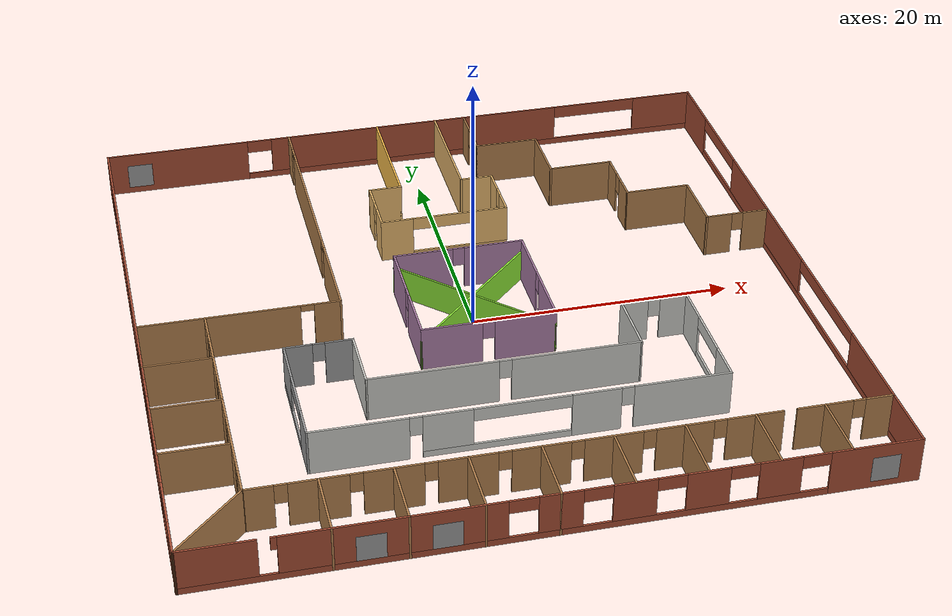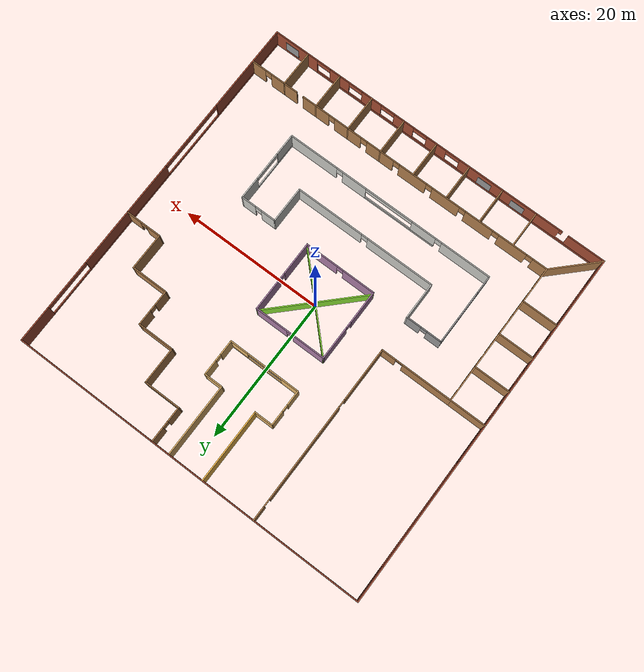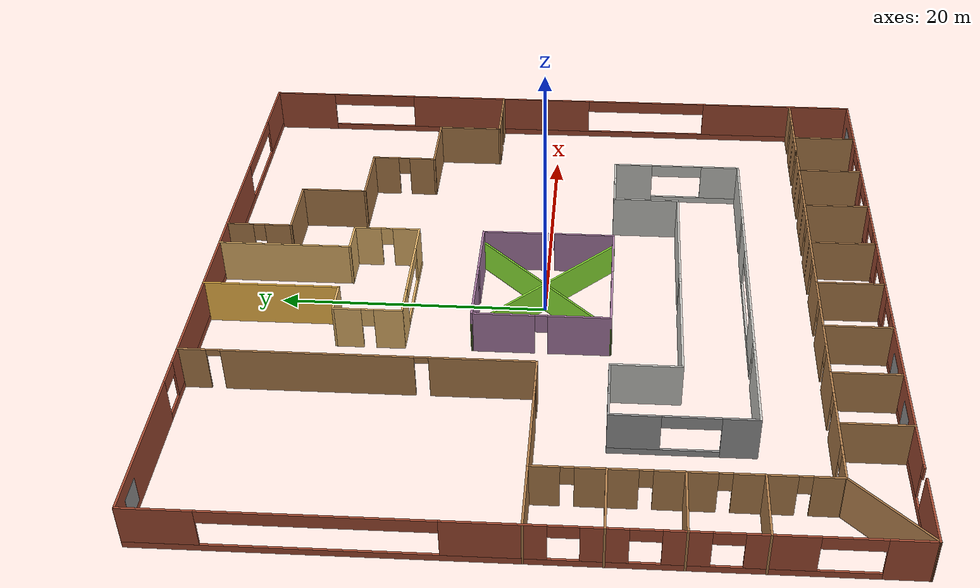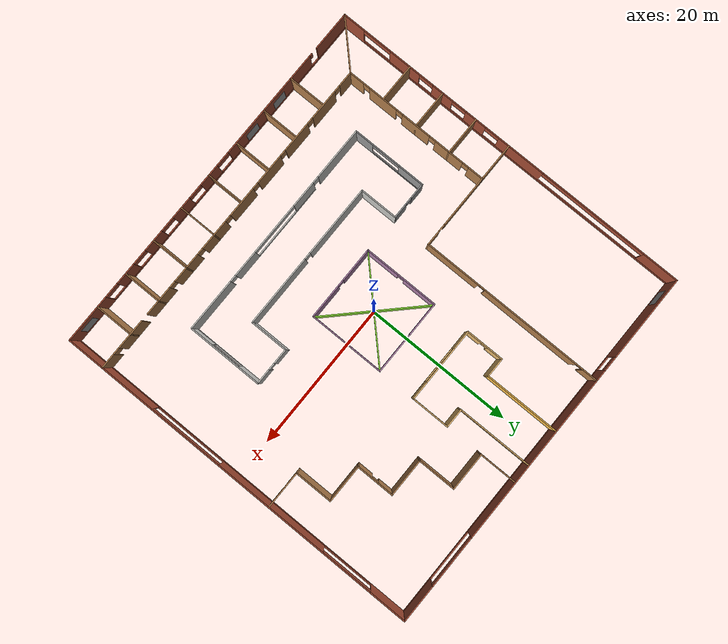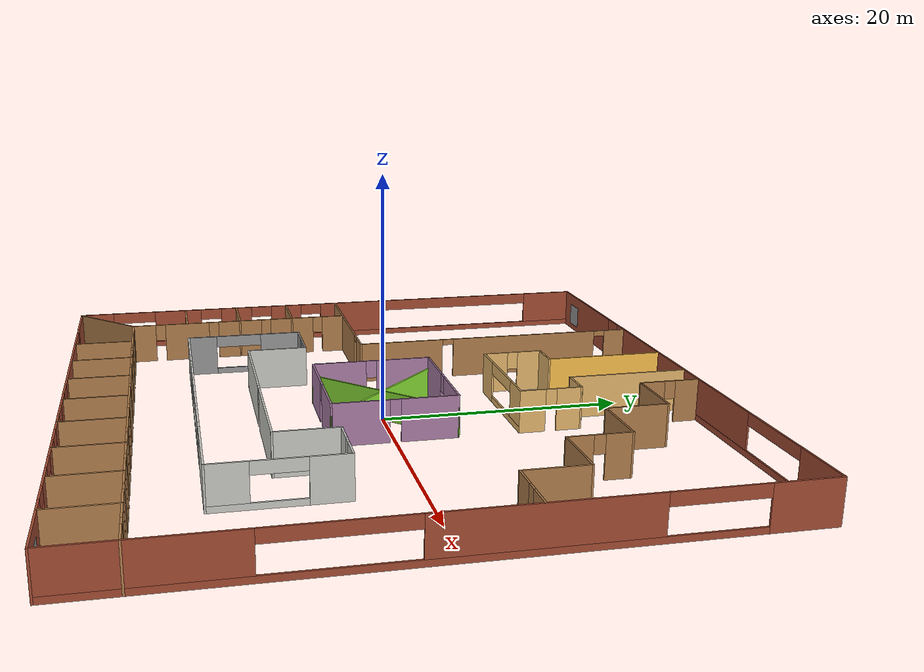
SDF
<?xml version='1.0'?>
<sdf version='1.7'>
  <model name='office__space'>
    <pose>-0.015532 -0.015532 0 0 -0 0</pose>
    <link name='Wall_0'>
      <pose>0.015532 25.0155 0 0 -0 0</pose>
      <visual name='Wall_0_Visual_0'>
        <pose>-19.2875 0 1.75 0 -0 0</pose>
        <geometry>
          <box>
            <size>11.575 0.15 3.5</size>
          </box>
        </geometry>
        <material>
          <script>
            <uri>file://media/materials/scripts/gazebo.material</uri>
            <name>Gazebo/Bricks</name>
          </script>
          <ambient>1 1 1 1</ambient>
        </material>
        <meta>
          <layer>0</layer>
        </meta>
      </visual>
      <collision name='Wall_0_Collision_0'>
        <geometry>
          <box>
            <size>11.575 0.15 3.5</size>
          </box>
        </geometry>
        <pose>-19.2875 0 1.75 0 -0 0</pose>
      </collision>
      <visual name='Wall_0_Visual_1'>
        <pose>5.7875 0 0.25 0 -0 0</pose>
        <geometry>
          <box>
            <size>38.575 0.15 0.5</size>
          </box>
        </geometry>
        <material>
          <script>
            <uri>file://media/materials/scripts/gazebo.material</uri>
            <name>Gazebo/Bricks</name>
          </script>
          <ambient>1 1 1 1</ambient>
        </material>
        <meta>
          <layer>0</layer>
        </meta>
      </visual>
      <collision name='Wall_0_Collision_1'>
        <geometry>
          <box>
            <size>38.575 0.15 0.5</size>
          </box>
        </geometry>
        <pose>5.7875 0 0.25 0 -0 0</pose>
      </collision>
      <visual name='Wall_0_Visual_2'>
        <pose>0.75 0 2 0 -0 0</pose>
        <geometry>
          <box>
            <size>24.5 0.15 3</size>
          </box>
        </geometry>
        <material>
          <script>
            <uri>file://media/materials/scripts/gazebo.material</uri>
            <name>Gazebo/Bricks</name>
          </script>
          <ambient>1 1 1 1</ambient>
        </material>
        <meta>
          <layer>0</layer>
        </meta>
      </visual>
      <collision name='Wall_0_Collision_2'>
        <geometry>
          <box>
            <size>24.5 0.15 3</size>
          </box>
        </geometry>
        <pose>0.75 0 2 0 -0 0</pose>
      </collision>
      <visual name='Wall_0_Visual_3'>
        <pose>22.5375 0 2 0 -0 0</pose>
        <geometry>
          <box>
            <size>5.075 0.15 3</size>
          </box>
        </geometry>
        <material>
          <script>
            <uri>file://media/materials/scripts/gazebo.material</uri>
            <name>Gazebo/Bricks</name>
          </script>
          <ambient>1 1 1 1</ambient>
        </material>
        <meta>
          <layer>0</layer>
        </meta>
      </visual>
      <collision name='Wall_0_Collision_3'>
        <geometry>
          <box>
            <size>5.075 0.15 3</size>
          </box>
        </geometry>
        <pose>22.5375 0 2 0 -0 0</pose>
      </collision>
      <visual name='Wall_0_Visual_4'>
        <pose>-12.5 0 3 0 -0 0</pose>
        <geometry>
          <box>
            <size>2 0.15 1</size>
          </box>
        </geometry>
        <material>
          <script>
            <uri>file://media/materials/scripts/gazebo.material</uri>
            <name>Gazebo/Bricks</name>
          </script>
          <ambient>1 1 1 1</ambient>
        </material>
        <meta>
          <layer>0</layer>
        </meta>
      </visual>
      <collision name='Wall_0_Collision_4'>
        <geometry>
          <box>
            <size>2 0.15 1</size>
          </box>
        </geometry>
        <pose>-12.5 0 3 0 -0 0</pose>
      </collision>
      <visual name='Wall_0_Visual_5'>
        <pose>16.5 0 3 0 -0 0</pose>
        <geometry>
          <box>
            <size>7 0.15 1</size>
          </box>
        </geometry>
        <material>
          <script>
            <uri>file://media/materials/scripts/gazebo.material</uri>
            <name>Gazebo/Bricks</name>
          </script>
          <ambient>1 1 1 1</ambient>
        </material>
        <meta>
          <layer>0</layer>
        </meta>
      </visual>
      <collision name='Wall_0_Collision_5'>
        <geometry>
          <box>
            <size>7 0.15 1</size>
          </box>
        </geometry>
        <pose>16.5 0 3 0 -0 0</pose>
      </collision>
    </link>
    <link name='Wall_1'>
      <pose>25.0155 0.015532 0 0 -0 -1.5708</pose>
      <visual name='Wall_1_Visual_0'>
        <pose>-22.5375 0 1.75 0 -0 0</pose>
        <geometry>
          <box>
            <size>5.075 0.15 3.5</size>
          </box>
        </geometry>
        <material>
          <script>
            <uri>file://media/materials/scripts/gazebo.material</uri>
            <name>Gazebo/Bricks</name>
          </script>
          <ambient>1 1 1 1</ambient>
        </material>
        <meta>
          <layer>0</layer>
        </meta>
      </visual>
      <collision name='Wall_1_Collision_0'>
        <geometry>
          <box>
            <size>5.075 0.15 3.5</size>
          </box>
        </geometry>
        <pose>-22.5375 0 1.75 0 -0 0</pose>
      </collision>
      <visual name='Wall_1_Visual_1'>
        <pose>2.5375 0 0.25 0 -0 0</pose>
        <geometry>
          <box>
            <size>45.075 0.15 0.5</size>
          </box>
        </geometry>
        <material>
          <script>
            <uri>file://media/materials/scripts/gazebo.material</uri>
            <name>Gazebo/Bricks</name>
          </script>
          <ambient>1 1 1 1</ambient>
        </material>
        <meta>
          <layer>0</layer>
        </meta>
      </visual>
      <collision name='Wall_1_Collision_1'>
        <geometry>
          <box>
            <size>45.075 0.15 0.5</size>
          </box>
        </geometry>
        <pose>2.5375 0 0.25 0 -0 0</pose>
      </collision>
      <visual name='Wall_1_Visual_2'>
        <pose>-5.25 0 2 0 -0 0</pose>
        <geometry>
          <box>
            <size>15.5 0.15 3</size>
          </box>
        </geometry>
        <material>
          <script>
            <uri>file://media/materials/scripts/gazebo.material</uri>
            <name>Gazebo/Bricks</name>
          </script>
          <ambient>1 1 1 1</ambient>
        </material>
        <meta>
          <layer>0</layer>
        </meta>
      </visual>
      <collision name='Wall_1_Collision_2'>
        <geometry>
          <box>
            <size>15.5 0.15 3</size>
          </box>
        </geometry>
        <pose>-5.25 0 2 0 -0 0</pose>
      </collision>
      <visual name='Wall_1_Visual_3'>
        <pose>18.7875 0 2 0 -0 0</pose>
        <geometry>
          <box>
            <size>12.575 0.15 3</size>
          </box>
        </geometry>
        <material>
          <script>
            <uri>file://media/materials/scripts/gazebo.material</uri>
            <name>Gazebo/Bricks</name>
          </script>
          <ambient>1 1 1 1</ambient>
        </material>
        <meta>
          <layer>0</layer>
        </meta>
      </visual>
      <collision name='Wall_1_Collision_3'>
        <geometry>
          <box>
            <size>12.575 0.15 3</size>
          </box>
        </geometry>
        <pose>18.7875 0 2 0 -0 0</pose>
      </collision>
      <visual name='Wall_1_Visual_4'>
        <pose>-16.5 0 3 0 -0 0</pose>
        <geometry>
          <box>
            <size>7 0.15 1</size>
          </box>
        </geometry>
        <material>
          <script>
            <uri>file://media/materials/scripts/gazebo.material</uri>
            <name>Gazebo/Bricks</name>
          </script>
          <ambient>1 1 1 1</ambient>
        </material>
        <meta>
          <layer>0</layer>
        </meta>
      </visual>
      <collision name='Wall_1_Collision_4'>
        <geometry>
          <box>
            <size>7 0.15 1</size>
          </box>
        </geometry>
        <pose>-16.5 0 3 0 -0 0</pose>
      </collision>
      <visual name='Wall_1_Visual_5'>
        <pose>7.5 0 3 0 -0 0</pose>
        <geometry>
          <box>
            <size>10 0.15 1</size>
          </box>
        </geometry>
        <material>
          <script>
            <uri>file://media/materials/scripts/gazebo.material</uri>
            <name>Gazebo/Bricks</name>
          </script>
          <ambient>1 1 1 1</ambient>
        </material>
        <meta>
          <layer>0</layer>
        </meta>
      </visual>
      <collision name='Wall_1_Collision_5'>
        <geometry>
          <box>
            <size>10 0.15 1</size>
          </box>
        </geometry>
        <pose>7.5 0 3 0 -0 0</pose>
      </collision>
    </link>
    <link name='Wall_12'>
      <collision name='Wall_12_Collision'>
        <geometry>
          <box>
            <size>5.15 0.15 3.5</size>
          </box>
        </geometry>
        <pose>0 0 1.75 0 -0 0</pose>
      </collision>
      <visual name='Wall_12_Visual'>
        <pose>0 0 1.75 0 -0 0</pose>
        <geometry>
          <box>
            <size>5.15 0.15 3.5</size>
          </box>
        </geometry>
        <material>
          <script>
            <uri>file://media/materials/scripts/gazebo.material</uri>
            <name>Gazebo/Wood</name>
          </script>
          <ambient>1 1 1 1</ambient>
        </material>
        <meta>
          <layer>0</layer>
        </meta>
      </visual>
      <pose>-22.4845 -4.98447 0 0 -0 0</pose>
    </link>
    <link name='Wall_14'>
      <collision name='Wall_14_Collision'>
        <geometry>
          <box>
            <size>5.15 0.15 3.5</size>
          </box>
        </geometry>
        <pose>0 0 1.75 0 -0 0</pose>
      </collision>
      <visual name='Wall_14_Visual'>
        <pose>0 0 1.75 0 -0 0</pose>
        <geometry>
          <box>
            <size>5.15 0.15 3.5</size>
          </box>
        </geometry>
        <material>
          <script>
            <uri>file://media/materials/scripts/gazebo.material</uri>
            <name>Gazebo/Wood</name>
          </script>
          <ambient>1 1 1 1</ambient>
        </material>
        <meta>
          <layer>0</layer>
        </meta>
      </visual>
      <pose>-22.4845 -9.98447 0 0 -0 0</pose>
    </link>
    <link name='Wall_16'>
      <collision name='Wall_16_Collision'>
        <geometry>
          <box>
            <size>5.15 0.15 3.5</size>
          </box>
        </geometry>
        <pose>0 0 1.75 0 -0 0</pose>
      </collision>
      <visual name='Wall_16_Visual'>
        <pose>0 0 1.75 0 -0 0</pose>
        <geometry>
          <box>
            <size>5.15 0.15 3.5</size>
          </box>
        </geometry>
        <material>
          <script>
            <uri>file://media/materials/scripts/gazebo.material</uri>
            <name>Gazebo/Wood</name>
          </script>
          <ambient>1 1 1 1</ambient>
        </material>
        <meta>
          <layer>0</layer>
        </meta>
      </visual>
      <pose>-22.4845 -14.9845 0 0 -0 0</pose>
    </link>
    <link name='Wall_19'>
      <collision name='Wall_19_Collision'>
        <geometry>
          <box>
            <size>7.22107 0.15 3.5</size>
          </box>
        </geometry>
        <pose>0 0 1.75 0 -0 0</pose>
      </collision>
      <visual name='Wall_19_Visual'>
        <pose>0 0 1.75 0 -0 0</pose>
        <geometry>
          <box>
            <size>7.22107 0.15 3.5</size>
          </box>
        </geometry>
        <material>
          <script>
            <uri>file://media/materials/scripts/gazebo.material</uri>
            <name>Gazebo/Wood</name>
          </script>
          <ambient>1 1 1 1</ambient>
        </material>
        <meta>
          <layer>0</layer>
        </meta>
      </visual>
      <pose>-22.4845 -22.4845 0 0 -0 -2.35619</pose>
    </link>
    <link name='Wall_2'>
      <pose>0.015532 -24.9845 0 0 -0 3.14159</pose>
      <visual name='Wall_2_Visual_0'>
        <pose>-21.7875 0 1.75 0 -0 0</pose>
        <geometry>
          <box>
            <size>6.575 0.15 3.5</size>
          </box>
        </geometry>
        <material>
          <script>
            <uri>file://media/materials/scripts/gazebo.material</uri>
            <name>Gazebo/Bricks</name>
          </script>
          <ambient>1 1 1 1</ambient>
        </material>
        <meta>
          <layer>0</layer>
        </meta>
      </visual>
      <collision name='Wall_2_Collision_0'>
        <geometry>
          <box>
            <size>6.575 0.15 3.5</size>
          </box>
        </geometry>
        <pose>-21.7875 0 1.75 0 -0 0</pose>
      </collision>
      <visual name='Wall_2_Visual_1'>
        <pose>3.2875 0 0.25 0 -0 0</pose>
        <geometry>
          <box>
            <size>43.575 0.15 0.5</size>
          </box>
        </geometry>
        <material>
          <script>
            <uri>file://media/materials/scripts/gazebo.material</uri>
            <name>Gazebo/Bricks</name>
          </script>
          <ambient>1 1 1 1</ambient>
        </material>
        <meta>
          <layer>0</layer>
        </meta>
      </visual>
      <collision name='Wall_2_Collision_1'>
        <geometry>
          <box>
            <size>43.575 0.15 0.5</size>
          </box>
        </geometry>
        <pose>3.2875 0 0.25 0 -0 0</pose>
      </collision>
      <visual name='Wall_2_Visual_2'>
        <pose>-15.0031 0 2 0 -0 0</pose>
        <geometry>
          <box>
            <size>2.99379 0.15 3</size>
          </box>
        </geometry>
        <material>
          <script>
            <uri>file://media/materials/scripts/gazebo.material</uri>
            <name>Gazebo/Bricks</name>
          </script>
          <ambient>1 1 1 1</ambient>
        </material>
        <meta>
          <layer>0</layer>
        </meta>
      </visual>
      <collision name='Wall_2_Collision_2'>
        <geometry>
          <box>
            <size>2.99379 0.15 3</size>
          </box>
        </geometry>
        <pose>-15.0031 0 2 0 -0 0</pose>
      </collision>
      <visual name='Wall_2_Visual_3'>
        <pose>-10.0031 0 2 0 -0 0</pose>
        <geometry>
          <box>
            <size>3.00621 0.15 3</size>
          </box>
        </geometry>
        <material>
          <script>
            <uri>file://media/materials/scripts/gazebo.material</uri>
            <name>Gazebo/Bricks</name>
          </script>
          <ambient>1 1 1 1</ambient>
        </material>
        <meta>
          <layer>0</layer>
        </meta>
      </visual>
      <collision name='Wall_2_Collision_3'>
        <geometry>
          <box>
            <size>3.00621 0.15 3</size>
          </box>
        </geometry>
        <pose>-10.0031 0 2 0 -0 0</pose>
      </collision>
      <visual name='Wall_2_Visual_4'>
        <pose>-5 0 2 0 -0 0</pose>
        <geometry>
          <box>
            <size>3 0.15 3</size>
          </box>
        </geometry>
        <material>
          <script>
            <uri>file://media/materials/scripts/gazebo.material</uri>
            <name>Gazebo/Bricks</name>
          </script>
          <ambient>1 1 1 1</ambient>
        </material>
        <meta>
          <layer>0</layer>
        </meta>
      </visual>
      <collision name='Wall_2_Collision_4'>
        <geometry>
          <box>
            <size>3 0.15 3</size>
          </box>
        </geometry>
        <pose>-5 0 2 0 -0 0</pose>
      </collision>
      <visual name='Wall_2_Visual_5'>
        <pose>0 0 2 0 -0 0</pose>
        <geometry>
          <box>
            <size>3 0.15 3</size>
          </box>
        </geometry>
        <material>
          <script>
            <uri>file://media/materials/scripts/gazebo.material</uri>
            <name>Gazebo/Bricks</name>
          </script>
          <ambient>1 1 1 1</ambient>
        </material>
        <meta>
          <layer>0</layer>
        </meta>
      </visual>
      <collision name='Wall_2_Collision_5'>
        <geometry>
          <box>
            <size>3 0.15 3</size>
          </box>
        </geometry>
        <pose>0 0 2 0 -0 0</pose>
      </collision>
      <visual name='Wall_2_Visual_6'>
        <pose>11 0 2 0 -0 0</pose>
        <geometry>
          <box>
            <size>15 0.15 3</size>
          </box>
        </geometry>
        <material>
          <script>
            <uri>file://media/materials/scripts/gazebo.material</uri>
            <name>Gazebo/Bricks</name>
          </script>
          <ambient>1 1 1 1</ambient>
        </material>
        <meta>
          <layer>0</layer>
        </meta>
      </visual>
      <collision name='Wall_2_Collision_6'>
        <geometry>
          <box>
            <size>15 0.15 3</size>
          </box>
        </geometry>
        <pose>11 0 2 0 -0 0</pose>
      </collision>
      <visual name='Wall_2_Visual_7'>
        <pose>22.3969 0 2 0 -0 0</pose>
        <geometry>
          <box>
            <size>5.35618 0.15 3</size>
          </box>
        </geometry>
        <material>
          <script>
            <uri>file://media/materials/scripts/gazebo.material</uri>
            <name>Gazebo/Bricks</name>
          </script>
          <ambient>1 1 1 1</ambient>
        </material>
        <meta>
          <layer>0</layer>
        </meta>
      </visual>
      <collision name='Wall_2_Collision_7'>
        <geometry>
          <box>
            <size>5.35618 0.15 3</size>
          </box>
        </geometry>
        <pose>22.3969 0 2 0 -0 0</pose>
      </collision>
      <visual name='Wall_2_Visual_8'>
        <pose>-17.5 0 3 0 -0 0</pose>
        <geometry>
          <box>
            <size>2 0.15 1</size>
          </box>
        </geometry>
        <material>
          <script>
            <uri>file://media/materials/scripts/gazebo.material</uri>
            <name>Gazebo/Bricks</name>
          </script>
          <ambient>1 1 1 1</ambient>
        </material>
        <meta>
          <layer>0</layer>
        </meta>
      </visual>
      <collision name='Wall_2_Collision_8'>
        <geometry>
          <box>
            <size>2 0.15 1</size>
          </box>
        </geometry>
        <pose>-17.5 0 3 0 -0 0</pose>
      </collision>
      <visual name='Wall_2_Visual_9'>
        <pose>-12.5062 0 3 0 -0 0</pose>
        <geometry>
          <box>
            <size>2 0.15 1</size>
          </box>
        </geometry>
        <material>
          <script>
            <uri>file://media/materials/scripts/gazebo.material</uri>
            <name>Gazebo/Bricks</name>
          </script>
          <ambient>1 1 1 1</ambient>
        </material>
        <meta>
          <layer>0</layer>
        </meta>
      </visual>
      <collision name='Wall_2_Collision_9'>
        <geometry>
          <box>
            <size>2 0.15 1</size>
          </box>
        </geometry>
        <pose>-12.5062 0 3 0 -0 0</pose>
      </collision>
      <visual name='Wall_2_Visual_10'>
        <pose>-7.5 0 3 0 -0 0</pose>
        <geometry>
          <box>
            <size>2 0.15 1</size>
          </box>
        </geometry>
        <material>
          <script>
            <uri>file://media/materials/scripts/gazebo.material</uri>
            <name>Gazebo/Bricks</name>
          </script>
          <ambient>1 1 1 1</ambient>
        </material>
        <meta>
          <layer>0</layer>
        </meta>
      </visual>
      <collision name='Wall_2_Collision_10'>
        <geometry>
          <box>
            <size>2 0.15 1</size>
          </box>
        </geometry>
        <pose>-7.5 0 3 0 -0 0</pose>
      </collision>
      <visual name='Wall_2_Visual_11'>
        <pose>-2.5 0 3 0 -0 0</pose>
        <geometry>
          <box>
            <size>2 0.15 1</size>
          </box>
        </geometry>
        <material>
          <script>
            <uri>file://media/materials/scripts/gazebo.material</uri>
            <name>Gazebo/Bricks</name>
          </script>
          <ambient>1 1 1 1</ambient>
        </material>
        <meta>
          <layer>0</layer>
        </meta>
      </visual>
      <collision name='Wall_2_Collision_11'>
        <geometry>
          <box>
            <size>2 0.15 1</size>
          </box>
        </geometry>
        <pose>-2.5 0 3 0 -0 0</pose>
      </collision>
      <visual name='Wall_2_Visual_12'>
        <pose>2.5 0 3 0 -0 0</pose>
        <geometry>
          <box>
            <size>2 0.15 1</size>
          </box>
        </geometry>
        <material>
          <script>
            <uri>file://media/materials/scripts/gazebo.material</uri>
            <name>Gazebo/Bricks</name>
          </script>
          <ambient>1 1 1 1</ambient>
        </material>
        <meta>
          <layer>0</layer>
        </meta>
      </visual>
      <collision name='Wall_2_Collision_12'>
        <geometry>
          <box>
            <size>2 0.15 1</size>
          </box>
        </geometry>
        <pose>2.5 0 3 0 -0 0</pose>
      </collision>
      <visual name='Wall_2_Visual_13'>
        <pose>18.7094 0 3 0 -0 0</pose>
        <geometry>
          <box>
            <size>0.418823 0.15 1</size>
          </box>
        </geometry>
        <material>
          <script>
            <uri>file://media/materials/scripts/gazebo.material</uri>
            <name>Gazebo/Bricks</name>
          </script>
          <ambient>1 1 1 1</ambient>
        </material>
        <meta>
          <layer>0</layer>
        </meta>
      </visual>
      <collision name='Wall_2_Collision_13'>
        <geometry>
          <box>
            <size>0.418823 0.15 1</size>
          </box>
        </geometry>
        <pose>18.7094 0 3 0 -0 0</pose>
      </collision>
    </link>
    <link name='Wall_21'>
      <collision name='Wall_21_Collision'>
        <geometry>
          <box>
            <size>5.15 0.15 3.5</size>
          </box>
        </geometry>
        <pose>0 0 1.75 0 -0 0</pose>
      </collision>
      <visual name='Wall_21_Visual'>
        <pose>0 0 1.75 0 -0 0</pose>
        <geometry>
          <box>
            <size>5.15 0.15 3.5</size>
          </box>
        </geometry>
        <material>
          <script>
            <uri>file://media/materials/scripts/gazebo.material</uri>
            <name>Gazebo/Wood</name>
          </script>
          <ambient>1 1 1 1</ambient>
        </material>
        <meta>
          <layer>0</layer>
        </meta>
      </visual>
      <pose>20.0155 -22.4845 0 0 -0 1.5708</pose>
    </link>
    <link name='Wall_23'>
      <collision name='Wall_23_Collision'>
        <geometry>
          <box>
            <size>5.15 0.15 3.5</size>
          </box>
        </geometry>
        <pose>0 0 1.75 0 -0 0</pose>
      </collision>
      <visual name='Wall_23_Visual'>
        <pose>0 0 1.75 0 -0 0</pose>
        <geometry>
          <box>
            <size>5.15 0.15 3.5</size>
          </box>
        </geometry>
        <material>
          <script>
            <uri>file://media/materials/scripts/gazebo.material</uri>
            <name>Gazebo/Wood</name>
          </script>
          <ambient>1 1 1 1</ambient>
        </material>
        <meta>
          <layer>0</layer>
        </meta>
      </visual>
      <pose>15.0155 -22.4845 0 0 -0 1.5708</pose>
    </link>
    <link name='Wall_25'>
      <collision name='Wall_25_Collision'>
        <geometry>
          <box>
            <size>5.15 0.15 3.5</size>
          </box>
        </geometry>
        <pose>0 0 1.75 0 -0 0</pose>
      </collision>
      <visual name='Wall_25_Visual'>
        <pose>0 0 1.75 0 -0 0</pose>
        <geometry>
          <box>
            <size>5.15 0.15 3.5</size>
          </box>
        </geometry>
        <material>
          <script>
            <uri>file://media/materials/scripts/gazebo.material</uri>
            <name>Gazebo/Wood</name>
          </script>
          <ambient>1 1 1 1</ambient>
        </material>
        <meta>
          <layer>0</layer>
        </meta>
      </visual>
      <pose>10.0155 -22.4845 0 0 -0 1.5708</pose>
    </link>
    <link name='Wall_27'>
      <collision name='Wall_27_Collision'>
        <geometry>
          <box>
            <size>5.15 0.15 3.5</size>
          </box>
        </geometry>
        <pose>0 0 1.75 0 -0 0</pose>
      </collision>
      <visual name='Wall_27_Visual'>
        <pose>0 0 1.75 0 -0 0</pose>
        <geometry>
          <box>
            <size>5.15 0.15 3.5</size>
          </box>
        </geometry>
        <material>
          <script>
            <uri>file://media/materials/scripts/gazebo.material</uri>
            <name>Gazebo/Wood</name>
          </script>
          <ambient>1 1 1 1</ambient>
        </material>
        <meta>
          <layer>0</layer>
        </meta>
      </visual>
      <pose>5.01553 -22.4845 0 0 -0 1.5708</pose>
    </link>
    <link name='Wall_29'>
      <collision name='Wall_29_Collision'>
        <geometry>
          <box>
            <size>5.15 0.15 3.5</size>
          </box>
        </geometry>
        <pose>0 0 1.75 0 -0 0</pose>
      </collision>
      <visual name='Wall_29_Visual'>
        <pose>0 0 1.75 0 -0 0</pose>
        <geometry>
          <box>
            <size>5.15 0.15 3.5</size>
          </box>
        </geometry>
        <material>
          <script>
            <uri>file://media/materials/scripts/gazebo.material</uri>
            <name>Gazebo/Wood</name>
          </script>
          <ambient>1 1 1 1</ambient>
        </material>
        <meta>
          <layer>0</layer>
        </meta>
      </visual>
      <pose>0.015532 -22.4845 0 0 -0 1.5708</pose>
    </link>
    <link name='Wall_3'>
      <pose>-24.9845 0.015532 0 0 -0 1.5708</pose>
      <visual name='Wall_3_Visual_0'>
        <pose>-23.5375 0 1.75 0 -0 0</pose>
        <geometry>
          <box>
            <size>3.075 0.15 3.5</size>
          </box>
        </geometry>
        <material>
          <script>
            <uri>file://media/materials/scripts/gazebo.material</uri>
            <name>Gazebo/Bricks</name>
          </script>
          <ambient>1 1 1 1</ambient>
        </material>
        <meta>
          <layer>0</layer>
        </meta>
      </visual>
      <collision name='Wall_3_Collision_0'>
        <geometry>
          <box>
            <size>3.075 0.15 3.5</size>
          </box>
        </geometry>
        <pose>-23.5375 0 1.75 0 -0 0</pose>
      </collision>
      <visual name='Wall_3_Visual_1'>
        <pose>1.5375 0 0.25 0 -0 0</pose>
        <geometry>
          <box>
            <size>47.075 0.15 0.5</size>
          </box>
        </geometry>
        <material>
          <script>
            <uri>file://media/materials/scripts/gazebo.material</uri>
            <name>Gazebo/Bricks</name>
          </script>
          <ambient>1 1 1 1</ambient>
        </material>
        <meta>
          <layer>0</layer>
        </meta>
      </visual>
      <collision name='Wall_3_Collision_1'>
        <geometry>
          <box>
            <size>47.075 0.15 0.5</size>
          </box>
        </geometry>
        <pose>1.5375 0 0.25 0 -0 0</pose>
      </collision>
      <visual name='Wall_3_Visual_2'>
        <pose>-15.75 0 2 0 -0 0</pose>
        <geometry>
          <box>
            <size>4.5 0.15 3</size>
          </box>
        </geometry>
        <material>
          <script>
            <uri>file://media/materials/scripts/gazebo.material</uri>
            <name>Gazebo/Bricks</name>
          </script>
          <ambient>1 1 1 1</ambient>
        </material>
        <meta>
          <layer>0</layer>
        </meta>
      </visual>
      <collision name='Wall_3_Collision_2'>
        <geometry>
          <box>
            <size>4.5 0.15 3</size>
          </box>
        </geometry>
        <pose>-15.75 0 2 0 -0 0</pose>
      </collision>
      <visual name='Wall_3_Visual_3'>
        <pose>-10 0 2 0 -0 0</pose>
        <geometry>
          <box>
            <size>3 0.15 3</size>
          </box>
        </geometry>
        <material>
          <script>
            <uri>file://media/materials/scripts/gazebo.material</uri>
            <name>Gazebo/Bricks</name>
          </script>
          <ambient>1 1 1 1</ambient>
        </material>
        <meta>
          <layer>0</layer>
        </meta>
      </visual>
      <collision name='Wall_3_Collision_3'>
        <geometry>
          <box>
            <size>3 0.15 3</size>
          </box>
        </geometry>
        <pose>-10 0 2 0 -0 0</pose>
      </collision>
      <visual name='Wall_3_Visual_4'>
        <pose>-5 0 2 0 -0 0</pose>
        <geometry>
          <box>
            <size>3 0.15 3</size>
          </box>
        </geometry>
        <material>
          <script>
            <uri>file://media/materials/scripts/gazebo.material</uri>
            <name>Gazebo/Bricks</name>
          </script>
          <ambient>1 1 1 1</ambient>
        </material>
        <meta>
          <layer>0</layer>
        </meta>
      </visual>
      <collision name='Wall_3_Collision_4'>
        <geometry>
          <box>
            <size>3 0.15 3</size>
          </box>
        </geometry>
        <pose>-5 0 2 0 -0 0</pose>
      </collision>
      <visual name='Wall_3_Visual_5'>
        <pose>1.81915 0 2 0 -0 0</pose>
        <geometry>
          <box>
            <size>6.63829 0.15 3</size>
          </box>
        </geometry>
        <material>
          <script>
            <uri>file://media/materials/scripts/gazebo.material</uri>
            <name>Gazebo/Bricks</name>
          </script>
          <ambient>1 1 1 1</ambient>
        </material>
        <meta>
          <layer>0</layer>
        </meta>
      </visual>
      <collision name='Wall_3_Collision_5'>
        <geometry>
          <box>
            <size>6.63829 0.15 3</size>
          </box>
        </geometry>
        <pose>1.81915 0 2 0 -0 0</pose>
      </collision>
      <visual name='Wall_3_Visual_6'>
        <pose>22.6066 0 2 0 -0 0</pose>
        <geometry>
          <box>
            <size>4.93671 0.15 3</size>
          </box>
        </geometry>
        <material>
          <script>
            <uri>file://media/materials/scripts/gazebo.material</uri>
            <name>Gazebo/Bricks</name>
          </script>
          <ambient>1 1 1 1</ambient>
        </material>
        <meta>
          <layer>0</layer>
        </meta>
      </visual>
      <collision name='Wall_3_Collision_6'>
        <geometry>
          <box>
            <size>4.93671 0.15 3</size>
          </box>
        </geometry>
        <pose>22.6066 0 2 0 -0 0</pose>
      </collision>
      <visual name='Wall_3_Visual_7'>
        <pose>-20 0 3 0 -0 0</pose>
        <geometry>
          <box>
            <size>4 0.15 1</size>
          </box>
        </geometry>
        <material>
          <script>
            <uri>file://media/materials/scripts/gazebo.material</uri>
            <name>Gazebo/Bricks</name>
          </script>
          <ambient>1 1 1 1</ambient>
        </material>
        <meta>
          <layer>0</layer>
        </meta>
      </visual>
      <collision name='Wall_3_Collision_7'>
        <geometry>
          <box>
            <size>4 0.15 1</size>
          </box>
        </geometry>
        <pose>-20 0 3 0 -0 0</pose>
      </collision>
      <visual name='Wall_3_Visual_8'>
        <pose>-12.5 0 3 0 -0 0</pose>
        <geometry>
          <box>
            <size>2 0.15 1</size>
          </box>
        </geometry>
        <material>
          <script>
            <uri>file://media/materials/scripts/gazebo.material</uri>
            <name>Gazebo/Bricks</name>
          </script>
          <ambient>1 1 1 1</ambient>
        </material>
        <meta>
          <layer>0</layer>
        </meta>
      </visual>
      <collision name='Wall_3_Collision_8'>
        <geometry>
          <box>
            <size>2 0.15 1</size>
          </box>
        </geometry>
        <pose>-12.5 0 3 0 -0 0</pose>
      </collision>
      <visual name='Wall_3_Visual_9'>
        <pose>-7.5 0 3 0 -0 0</pose>
        <geometry>
          <box>
            <size>2 0.15 1</size>
          </box>
        </geometry>
        <material>
          <script>
            <uri>file://media/materials/scripts/gazebo.material</uri>
            <name>Gazebo/Bricks</name>
          </script>
          <ambient>1 1 1 1</ambient>
        </material>
        <meta>
          <layer>0</layer>
        </meta>
      </visual>
      <collision name='Wall_3_Collision_9'>
        <geometry>
          <box>
            <size>2 0.15 1</size>
          </box>
        </geometry>
        <pose>-7.5 0 3 0 -0 0</pose>
      </collision>
      <visual name='Wall_3_Visual_10'>
        <pose>-2.5 0 3 0 -0 0</pose>
        <geometry>
          <box>
            <size>2 0.15 1</size>
          </box>
        </geometry>
        <material>
          <script>
            <uri>file://media/materials/scripts/gazebo.material</uri>
            <name>Gazebo/Bricks</name>
          </script>
          <ambient>1 1 1 1</ambient>
        </material>
        <meta>
          <layer>0</layer>
        </meta>
      </visual>
      <collision name='Wall_3_Collision_10'>
        <geometry>
          <box>
            <size>2 0.15 1</size>
          </box>
        </geometry>
        <pose>-2.5 0 3 0 -0 0</pose>
      </collision>
      <visual name='Wall_3_Visual_11'>
        <pose>12.6383 0 3 0 -0 0</pose>
        <geometry>
          <box>
            <size>15 0.15 1</size>
          </box>
        </geometry>
        <material>
          <script>
            <uri>file://media/materials/scripts/gazebo.material</uri>
            <name>Gazebo/Bricks</name>
          </script>
          <ambient>1 1 1 1</ambient>
        </material>
        <meta>
          <layer>0</layer>
        </meta>
      </visual>
      <collision name='Wall_3_Collision_11'>
        <geometry>
          <box>
            <size>15 0.15 1</size>
          </box>
        </geometry>
        <pose>12.6383 0 3 0 -0 0</pose>
      </collision>
    </link>
    <link name='Wall_31'>
      <collision name='Wall_31_Collision'>
        <geometry>
          <box>
            <size>5.15 0.15 3.5</size>
          </box>
        </geometry>
        <pose>0 0 1.75 0 -0 0</pose>
      </collision>
      <visual name='Wall_31_Visual'>
        <pose>0 0 1.75 0 -0 0</pose>
        <geometry>
          <box>
            <size>5.15 0.15 3.5</size>
          </box>
        </geometry>
        <material>
          <script>
            <uri>file://media/materials/scripts/gazebo.material</uri>
            <name>Gazebo/Wood</name>
          </script>
          <ambient>1 1 1 1</ambient>
        </material>
        <meta>
          <layer>0</layer>
        </meta>
      </visual>
      <pose>-4.98447 -22.4845 0 0 -0 1.5708</pose>
    </link>
    <link name='Wall_33'>
      <collision name='Wall_33_Collision'>
        <geometry>
          <box>
            <size>5.15 0.15 3.5</size>
          </box>
        </geometry>
        <pose>0 0 1.75 0 -0 0</pose>
      </collision>
      <visual name='Wall_33_Visual'>
        <pose>0 0 1.75 0 -0 0</pose>
        <geometry>
          <box>
            <size>5.15 0.15 3.5</size>
          </box>
        </geometry>
        <material>
          <script>
            <uri>file://media/materials/scripts/gazebo.material</uri>
            <name>Gazebo/Wood</name>
          </script>
          <ambient>1 1 1 1</ambient>
        </material>
        <meta>
          <layer>0</layer>
        </meta>
      </visual>
      <pose>-9.98447 -22.4845 0 0 -0 1.5708</pose>
    </link>
    <link name='Wall_35'>
      <collision name='Wall_35_Collision'>
        <geometry>
          <box>
            <size>5.15 0.15 3.5</size>
          </box>
        </geometry>
        <pose>0 0 1.75 0 -0 0</pose>
      </collision>
      <visual name='Wall_35_Visual'>
        <pose>0 0 1.75 0 -0 0</pose>
        <geometry>
          <box>
            <size>5.15 0.15 3.5</size>
          </box>
        </geometry>
        <material>
          <script>
            <uri>file://media/materials/scripts/gazebo.material</uri>
            <name>Gazebo/Wood</name>
          </script>
          <ambient>1 1 1 1</ambient>
        </material>
        <meta>
          <layer>0</layer>
        </meta>
      </visual>
      <pose>-14.9845 -22.4845 0 0 -0 -1.5708</pose>
    </link>
    <link name='Wall_37'>
      <pose>0.015532 5.01553 0 0 -0 0</pose>
      <visual name='Wall_37_Visual_0'>
        <pose>-2.7625 0 1.75 0 -0 0</pose>
        <geometry>
          <box>
            <size>4.625 0.15 3.5</size>
          </box>
        </geometry>
        <material>
          <script>
            <uri>file://media/materials/scripts/gazebo.material</uri>
            <name>Gazebo/Grey</name>
          </script>
          <ambient>0.678431 0.498039 0.658824 1</ambient>
        </material>
        <meta>
          <layer>0</layer>
        </meta>
      </visual>
      <collision name='Wall_37_Collision_0'>
        <geometry>
          <box>
            <size>4.625 0.15 3.5</size>
          </box>
        </geometry>
        <pose>-2.7625 0 1.75 0 -0 0</pose>
      </collision>
      <visual name='Wall_37_Visual_1'>
        <pose>2.7625 0 1.75 0 -0 0</pose>
        <geometry>
          <box>
            <size>4.625 0.15 3.5</size>
          </box>
        </geometry>
        <material>
          <script>
            <uri>file://media/materials/scripts/gazebo.material</uri>
            <name>Gazebo/Grey</name>
          </script>
          <ambient>0.678431 0.498039 0.658824 1</ambient>
        </material>
        <meta>
          <layer>0</layer>
        </meta>
      </visual>
      <collision name='Wall_37_Collision_1'>
        <geometry>
          <box>
            <size>4.625 0.15 3.5</size>
          </box>
        </geometry>
        <pose>2.7625 0 1.75 0 -0 0</pose>
      </collision>
      <visual name='Wall_37_Visual_2'>
        <pose>0 0 2.75 0 -0 0</pose>
        <geometry>
          <box>
            <size>0.9 0.15 1.5</size>
          </box>
        </geometry>
        <material>
          <script>
            <uri>file://media/materials/scripts/gazebo.material</uri>
            <name>Gazebo/Grey</name>
          </script>
          <ambient>0.678431 0.498039 0.658824 1</ambient>
        </material>
        <meta>
          <layer>0</layer>
        </meta>
      </visual>
      <collision name='Wall_37_Collision_2'>
        <geometry>
          <box>
            <size>0.9 0.15 1.5</size>
          </box>
        </geometry>
        <pose>0 0 2.75 0 -0 0</pose>
      </collision>
    </link>
    <link name='Wall_38'>
      <collision name='Wall_38_Collision'>
        <geometry>
          <box>
            <size>14.2921 0.15 2.5</size>
          </box>
        </geometry>
        <pose>0 0 1.25 0 -0 0</pose>
      </collision>
      <visual name='Wall_38_Visual'>
        <pose>0 0 1.25 0 -0 0</pose>
        <geometry>
          <box>
            <size>14.2921 0.15 2.5</size>
          </box>
        </geometry>
        <material>
          <script>
            <uri>file://media/materials/scripts/gazebo.material</uri>
            <name>Gazebo/Grey</name>
          </script>
          <ambient>0.541176 0.886275 0.203922 1</ambient>
        </material>
        <meta>
          <layer>0</layer>
        </meta>
      </visual>
      <pose>0.015532 0.015532 0 0 -0 -2.35619</pose>
    </link>
    <link name='Wall_39'>
      <pose>0.015532 -4.98447 0 0 -0 0</pose>
      <visual name='Wall_39_Visual_0'>
        <pose>-2.7625 0 1.75 0 -0 0</pose>
        <geometry>
          <box>
            <size>4.625 0.15 3.5</size>
          </box>
        </geometry>
        <material>
          <script>
            <uri>file://media/materials/scripts/gazebo.material</uri>
            <name>Gazebo/Grey</name>
          </script>
          <ambient>0.678431 0.498039 0.658824 1</ambient>
        </material>
        <meta>
          <layer>0</layer>
        </meta>
      </visual>
      <collision name='Wall_39_Collision_0'>
        <geometry>
          <box>
            <size>4.625 0.15 3.5</size>
          </box>
        </geometry>
        <pose>-2.7625 0 1.75 0 -0 0</pose>
      </collision>
      <visual name='Wall_39_Visual_1'>
        <pose>2.7625 0 1.75 0 -0 0</pose>
        <geometry>
          <box>
            <size>4.625 0.15 3.5</size>
          </box>
        </geometry>
        <material>
          <script>
            <uri>file://media/materials/scripts/gazebo.material</uri>
            <name>Gazebo/Grey</name>
          </script>
          <ambient>0.678431 0.498039 0.658824 1</ambient>
        </material>
        <meta>
          <layer>0</layer>
        </meta>
      </visual>
      <collision name='Wall_39_Collision_1'>
        <geometry>
          <box>
            <size>4.625 0.15 3.5</size>
          </box>
        </geometry>
        <pose>2.7625 0 1.75 0 -0 0</pose>
      </collision>
      <visual name='Wall_39_Visual_2'>
        <pose>0 0 2.75 0 -0 0</pose>
        <geometry>
          <box>
            <size>0.9 0.15 1.5</size>
          </box>
        </geometry>
        <material>
          <script>
            <uri>file://media/materials/scripts/gazebo.material</uri>
            <name>Gazebo/Grey</name>
          </script>
          <ambient>0.678431 0.498039 0.658824 1</ambient>
        </material>
        <meta>
          <layer>0</layer>
        </meta>
      </visual>
      <collision name='Wall_39_Collision_2'>
        <geometry>
          <box>
            <size>0.9 0.15 1.5</size>
          </box>
        </geometry>
        <pose>0 0 2.75 0 -0 0</pose>
      </collision>
    </link>
    <link name='Wall_40'>
      <collision name='Wall_40_Collision'>
        <geometry>
          <box>
            <size>14.2921 0.15 2.5</size>
          </box>
        </geometry>
        <pose>0 0 1.25 0 -0 0</pose>
      </collision>
      <visual name='Wall_40_Visual'>
        <pose>0 0 1.25 0 -0 0</pose>
        <geometry>
          <box>
            <size>14.2921 0.15 2.5</size>
          </box>
        </geometry>
        <material>
          <script>
            <uri>file://media/materials/scripts/gazebo.material</uri>
            <name>Gazebo/Grey</name>
          </script>
          <ambient>0.541176 0.886275 0.203922 1</ambient>
        </material>
        <meta>
          <layer>0</layer>
        </meta>
      </visual>
      <pose>0.015532 0.015532 0 0 -0 2.35619</pose>
    </link>
    <link name='Wall_41'>
      <pose>-4.98447 0.015532 0 0 -0 -1.5708</pose>
      <visual name='Wall_41_Visual_0'>
        <pose>-2.7625 0 1.75 0 -0 0</pose>
        <geometry>
          <box>
            <size>4.625 0.15 3.5</size>
          </box>
        </geometry>
        <material>
          <script>
            <uri>file://media/materials/scripts/gazebo.material</uri>
            <name>Gazebo/Grey</name>
          </script>
          <ambient>0.678431 0.498039 0.658824 1</ambient>
        </material>
        <meta>
          <layer>0</layer>
        </meta>
      </visual>
      <collision name='Wall_41_Collision_0'>
        <geometry>
          <box>
            <size>4.625 0.15 3.5</size>
          </box>
        </geometry>
        <pose>-2.7625 0 1.75 0 -0 0</pose>
      </collision>
      <visual name='Wall_41_Visual_1'>
        <pose>2.7625 0 1.75 0 -0 0</pose>
        <geometry>
          <box>
            <size>4.625 0.15 3.5</size>
          </box>
        </geometry>
        <material>
          <script>
            <uri>file://media/materials/scripts/gazebo.material</uri>
            <name>Gazebo/Grey</name>
          </script>
          <ambient>0.678431 0.498039 0.658824 1</ambient>
        </material>
        <meta>
          <layer>0</layer>
        </meta>
      </visual>
      <collision name='Wall_41_Collision_1'>
        <geometry>
          <box>
            <size>4.625 0.15 3.5</size>
          </box>
        </geometry>
        <pose>2.7625 0 1.75 0 -0 0</pose>
      </collision>
      <visual name='Wall_41_Visual_2'>
        <pose>0 0 2.75 0 -0 0</pose>
        <geometry>
          <box>
            <size>0.9 0.15 1.5</size>
          </box>
        </geometry>
        <material>
          <script>
            <uri>file://media/materials/scripts/gazebo.material</uri>
            <name>Gazebo/Grey</name>
          </script>
          <ambient>0.678431 0.498039 0.658824 1</ambient>
        </material>
        <meta>
          <layer>0</layer>
        </meta>
      </visual>
      <collision name='Wall_41_Collision_2'>
        <geometry>
          <box>
            <size>0.9 0.15 1.5</size>
          </box>
        </geometry>
        <pose>0 0 2.75 0 -0 0</pose>
      </collision>
    </link>
    <link name='Wall_43'>
      <pose>5.01553 0.015532 0 0 -0 -1.5708</pose>
      <visual name='Wall_43_Visual_0'>
        <pose>-2.7625 0 1.75 0 -0 0</pose>
        <geometry>
          <box>
            <size>4.625 0.15 3.5</size>
          </box>
        </geometry>
        <material>
          <script>
            <uri>file://media/materials/scripts/gazebo.material</uri>
            <name>Gazebo/Grey</name>
          </script>
          <ambient>0.678431 0.498039 0.658824 1</ambient>
        </material>
        <meta>
          <layer>0</layer>
        </meta>
      </visual>
      <collision name='Wall_43_Collision_0'>
        <geometry>
          <box>
            <size>4.625 0.15 3.5</size>
          </box>
        </geometry>
        <pose>-2.7625 0 1.75 0 -0 0</pose>
      </collision>
      <visual name='Wall_43_Visual_1'>
        <pose>2.7625 0 1.75 0 -0 0</pose>
        <geometry>
          <box>
            <size>4.625 0.15 3.5</size>
          </box>
        </geometry>
        <material>
          <script>
            <uri>file://media/materials/scripts/gazebo.material</uri>
            <name>Gazebo/Grey</name>
          </script>
          <ambient>0.678431 0.498039 0.658824 1</ambient>
        </material>
        <meta>
          <layer>0</layer>
        </meta>
      </visual>
      <collision name='Wall_43_Collision_1'>
        <geometry>
          <box>
            <size>4.625 0.15 3.5</size>
          </box>
        </geometry>
        <pose>2.7625 0 1.75 0 -0 0</pose>
      </collision>
      <visual name='Wall_43_Visual_2'>
        <pose>0 0 2.75 0 -0 0</pose>
        <geometry>
          <box>
            <size>0.9 0.15 1.5</size>
          </box>
        </geometry>
        <material>
          <script>
            <uri>file://media/materials/scripts/gazebo.material</uri>
            <name>Gazebo/Grey</name>
          </script>
          <ambient>0.678431 0.498039 0.658824 1</ambient>
        </material>
        <meta>
          <layer>0</layer>
        </meta>
      </visual>
      <collision name='Wall_43_Collision_2'>
        <geometry>
          <box>
            <size>0.9 0.15 1.5</size>
          </box>
        </geometry>
        <pose>0 0 2.75 0 -0 0</pose>
      </collision>
    </link>
    <link name='Wall_45'>
      <pose>-9.98447 12.5155 0 0 -0 -1.5708</pose>
      <visual name='Wall_45_Visual_0'>
        <pose>-11.5375 0 1.75 0 -0 0</pose>
        <geometry>
          <box>
            <size>2.075 0.15 3.5</size>
          </box>
        </geometry>
        <material>
          <script>
            <uri>file://media/materials/scripts/gazebo.material</uri>
            <name>Gazebo/Wood</name>
          </script>
          <ambient>1 1 1 1</ambient>
        </material>
        <meta>
          <layer>0</layer>
        </meta>
      </visual>
      <collision name='Wall_45_Collision_0'>
        <geometry>
          <box>
            <size>2.075 0.15 3.5</size>
          </box>
        </geometry>
        <pose>-11.5375 0 1.75 0 -0 0</pose>
      </collision>
      <visual name='Wall_45_Visual_1'>
        <pose>-2.75 0 1.75 0 -0 0</pose>
        <geometry>
          <box>
            <size>13.5 0.15 3.5</size>
          </box>
        </geometry>
        <material>
          <script>
            <uri>file://media/materials/scripts/gazebo.material</uri>
            <name>Gazebo/Wood</name>
          </script>
          <ambient>1 1 1 1</ambient>
        </material>
        <meta>
          <layer>0</layer>
        </meta>
      </visual>
      <collision name='Wall_45_Collision_1'>
        <geometry>
          <box>
            <size>13.5 0.15 3.5</size>
          </box>
        </geometry>
        <pose>-2.75 0 1.75 0 -0 0</pose>
      </collision>
      <visual name='Wall_45_Visual_2'>
        <pose>8.7875 0 1.75 0 -0 0</pose>
        <geometry>
          <box>
            <size>7.575 0.15 3.5</size>
          </box>
        </geometry>
        <material>
          <script>
            <uri>file://media/materials/scripts/gazebo.material</uri>
            <name>Gazebo/Wood</name>
          </script>
          <ambient>1 1 1 1</ambient>
        </material>
        <meta>
          <layer>0</layer>
        </meta>
      </visual>
      <collision name='Wall_45_Collision_2'>
        <geometry>
          <box>
            <size>7.575 0.15 3.5</size>
          </box>
        </geometry>
        <pose>8.7875 0 1.75 0 -0 0</pose>
      </collision>
      <visual name='Wall_45_Visual_3'>
        <pose>-10 0 3.25 0 -0 0</pose>
        <geometry>
          <box>
            <size>1 0.15 0.5</size>
          </box>
        </geometry>
        <material>
          <script>
            <uri>file://media/materials/scripts/gazebo.material</uri>
            <name>Gazebo/Wood</name>
          </script>
          <ambient>1 1 1 1</ambient>
        </material>
        <meta>
          <layer>0</layer>
        </meta>
      </visual>
      <collision name='Wall_45_Collision_3'>
        <geometry>
          <box>
            <size>1 0.15 0.5</size>
          </box>
        </geometry>
        <pose>-10 0 3.25 0 -0 0</pose>
      </collision>
      <visual name='Wall_45_Visual_4'>
        <pose>4.5 0 3.25 0 -0 0</pose>
        <geometry>
          <box>
            <size>1 0.15 0.5</size>
          </box>
        </geometry>
        <material>
          <script>
            <uri>file://media/materials/scripts/gazebo.material</uri>
            <name>Gazebo/Wood</name>
          </script>
          <ambient>1 1 1 1</ambient>
        </material>
        <meta>
          <layer>0</layer>
        </meta>
      </visual>
      <collision name='Wall_45_Collision_4'>
        <geometry>
          <box>
            <size>1 0.15 0.5</size>
          </box>
        </geometry>
        <pose>4.5 0 3.25 0 -0 0</pose>
      </collision>
    </link>
    <link name='Wall_46'>
      <pose>-14.9845 0.015532 0 0 -0 3.14159</pose>
      <visual name='Wall_46_Visual_0'>
        <pose>-4.0375 0 1.75 0 -0 0</pose>
        <geometry>
          <box>
            <size>2.075 0.15 3.5</size>
          </box>
        </geometry>
        <material>
          <script>
            <uri>file://media/materials/scripts/gazebo.material</uri>
            <name>Gazebo/Wood</name>
          </script>
          <ambient>1 1 1 1</ambient>
        </material>
        <meta>
          <layer>0</layer>
        </meta>
      </visual>
      <collision name='Wall_46_Collision_0'>
        <geometry>
          <box>
            <size>2.075 0.15 3.5</size>
          </box>
        </geometry>
        <pose>-4.0375 0 1.75 0 -0 0</pose>
      </collision>
      <visual name='Wall_46_Visual_1'>
        <pose>1.5375 0 1.75 0 -0 0</pose>
        <geometry>
          <box>
            <size>7.075 0.15 3.5</size>
          </box>
        </geometry>
        <material>
          <script>
            <uri>file://media/materials/scripts/gazebo.material</uri>
            <name>Gazebo/Wood</name>
          </script>
          <ambient>1 1 1 1</ambient>
        </material>
        <meta>
          <layer>0</layer>
        </meta>
      </visual>
      <collision name='Wall_46_Collision_1'>
        <geometry>
          <box>
            <size>7.075 0.15 3.5</size>
          </box>
        </geometry>
        <pose>1.5375 0 1.75 0 -0 0</pose>
      </collision>
      <visual name='Wall_46_Visual_2'>
        <pose>-2.5 0 3.25 0 -0 0</pose>
        <geometry>
          <box>
            <size>1 0.15 0.5</size>
          </box>
        </geometry>
        <material>
          <script>
            <uri>file://media/materials/scripts/gazebo.material</uri>
            <name>Gazebo/Wood</name>
          </script>
          <ambient>1 1 1 1</ambient>
        </material>
        <meta>
          <layer>0</layer>
        </meta>
      </visual>
      <collision name='Wall_46_Collision_2'>
        <geometry>
          <box>
            <size>1 0.15 0.5</size>
          </box>
        </geometry>
        <pose>-2.5 0 3.25 0 -0 0</pose>
      </collision>
    </link>
    <link name='Wall_49'>
      <pose>22.5155 5.01553 0 0 -0 3.14159</pose>
      <visual name='Wall_49_Visual_0'>
        <pose>-1.5125 0 1.75 0 -0 0</pose>
        <geometry>
          <box>
            <size>2.125 0.15 3.5</size>
          </box>
        </geometry>
        <material>
          <script>
            <uri>file://media/materials/scripts/gazebo.material</uri>
            <name>Gazebo/Wood</name>
          </script>
          <ambient>1 1 1 1</ambient>
        </material>
        <meta>
          <layer>0</layer>
        </meta>
      </visual>
      <collision name='Wall_49_Collision_0'>
        <geometry>
          <box>
            <size>2.125 0.15 3.5</size>
          </box>
        </geometry>
        <pose>-1.5125 0 1.75 0 -0 0</pose>
      </collision>
      <visual name='Wall_49_Visual_1'>
        <pose>1.5125 0 1.75 0 -0 0</pose>
        <geometry>
          <box>
            <size>2.125 0.15 3.5</size>
          </box>
        </geometry>
        <material>
          <script>
            <uri>file://media/materials/scripts/gazebo.material</uri>
            <name>Gazebo/Wood</name>
          </script>
          <ambient>1 1 1 1</ambient>
        </material>
        <meta>
          <layer>0</layer>
        </meta>
      </visual>
      <collision name='Wall_49_Collision_1'>
        <geometry>
          <box>
            <size>2.125 0.15 3.5</size>
          </box>
        </geometry>
        <pose>1.5125 0 1.75 0 -0 0</pose>
      </collision>
      <visual name='Wall_49_Visual_2'>
        <pose>-0 0 2.75 0 -0 0</pose>
        <geometry>
          <box>
            <size>0.9 0.15 1.5</size>
          </box>
        </geometry>
        <material>
          <script>
            <uri>file://media/materials/scripts/gazebo.material</uri>
            <name>Gazebo/Wood</name>
          </script>
          <ambient>1 1 1 1</ambient>
        </material>
        <meta>
          <layer>0</layer>
        </meta>
      </visual>
      <collision name='Wall_49_Collision_2'>
        <geometry>
          <box>
            <size>0.9 0.15 1.5</size>
          </box>
        </geometry>
        <pose>-0 0 2.75 0 -0 0</pose>
      </collision>
    </link>
    <link name='Wall_50'>
      <collision name='Wall_50_Collision'>
        <geometry>
          <box>
            <size>5.15 0.15 3.5</size>
          </box>
        </geometry>
        <pose>0 0 1.75 0 -0 0</pose>
      </collision>
      <visual name='Wall_50_Visual'>
        <pose>0 0 1.75 0 -0 0</pose>
        <geometry>
          <box>
            <size>5.15 0.15 3.5</size>
          </box>
        </geometry>
        <material>
          <script>
            <uri>file://media/materials/scripts/gazebo.material</uri>
            <name>Gazebo/Wood</name>
          </script>
          <ambient>1 1 1 1</ambient>
        </material>
        <meta>
          <layer>0</layer>
        </meta>
      </visual>
      <pose>20.0155 7.51553 0 0 -0 1.5708</pose>
    </link>
    <link name='Wall_51'>
      <collision name='Wall_51_Collision'>
        <geometry>
          <box>
            <size>5.15 0.15 3.5</size>
          </box>
        </geometry>
        <pose>0 0 1.75 0 -0 0</pose>
      </collision>
      <visual name='Wall_51_Visual'>
        <pose>0 0 1.75 0 -0 0</pose>
        <geometry>
          <box>
            <size>5.15 0.15 3.5</size>
          </box>
        </geometry>
        <material>
          <script>
            <uri>file://media/materials/scripts/gazebo.material</uri>
            <name>Gazebo/Wood</name>
          </script>
          <ambient>1 1 1 1</ambient>
        </material>
        <meta>
          <layer>0</layer>
        </meta>
      </visual>
      <pose>17.5155 10.0155 0 0 -0 3.14159</pose>
    </link>
    <link name='Wall_52'>
      <pose>15.0155 12.5155 0 0 -0 1.5708</pose>
      <visual name='Wall_52_Visual_0'>
        <pose>-1.5125 0 1.75 0 -0 0</pose>
        <geometry>
          <box>
            <size>2.125 0.15 3.5</size>
          </box>
        </geometry>
        <material>
          <script>
            <uri>file://media/materials/scripts/gazebo.material</uri>
            <name>Gazebo/Wood</name>
          </script>
          <ambient>1 1 1 1</ambient>
        </material>
        <meta>
          <layer>0</layer>
        </meta>
      </visual>
      <collision name='Wall_52_Collision_0'>
        <geometry>
          <box>
            <size>2.125 0.15 3.5</size>
          </box>
        </geometry>
        <pose>-1.5125 0 1.75 0 -0 0</pose>
      </collision>
      <visual name='Wall_52_Visual_1'>
        <pose>1.5125 0 1.75 0 -0 0</pose>
        <geometry>
          <box>
            <size>2.125 0.15 3.5</size>
          </box>
        </geometry>
        <material>
          <script>
            <uri>file://media/materials/scripts/gazebo.material</uri>
            <name>Gazebo/Wood</name>
          </script>
          <ambient>1 1 1 1</ambient>
        </material>
        <meta>
          <layer>0</layer>
        </meta>
      </visual>
      <collision name='Wall_52_Collision_1'>
        <geometry>
          <box>
            <size>2.125 0.15 3.5</size>
          </box>
        </geometry>
        <pose>1.5125 0 1.75 0 -0 0</pose>
      </collision>
      <visual name='Wall_52_Visual_2'>
        <pose>-0 0 2.75 0 -0 0</pose>
        <geometry>
          <box>
            <size>0.9 0.15 1.5</size>
          </box>
        </geometry>
        <material>
          <script>
            <uri>file://media/materials/scripts/gazebo.material</uri>
            <name>Gazebo/Wood</name>
          </script>
          <ambient>1 1 1 1</ambient>
        </material>
        <meta>
          <layer>0</layer>
        </meta>
      </visual>
      <collision name='Wall_52_Collision_2'>
        <geometry>
          <box>
            <size>0.9 0.15 1.5</size>
          </box>
        </geometry>
        <pose>-0 0 2.75 0 -0 0</pose>
      </collision>
    </link>
    <link name='Wall_53'>
      <collision name='Wall_53_Collision'>
        <geometry>
          <box>
            <size>5.15 0.15 3.5</size>
          </box>
        </geometry>
        <pose>0 0 1.75 0 -0 0</pose>
      </collision>
      <visual name='Wall_53_Visual'>
        <pose>0 0 1.75 0 -0 0</pose>
        <geometry>
          <box>
            <size>5.15 0.15 3.5</size>
          </box>
        </geometry>
        <material>
          <script>
            <uri>file://media/materials/scripts/gazebo.material</uri>
            <name>Gazebo/Wood</name>
          </script>
          <ambient>1 1 1 1</ambient>
        </material>
        <meta>
          <layer>0</layer>
        </meta>
      </visual>
      <pose>12.5155 15.0155 0 0 -0 3.14159</pose>
    </link>
    <link name='Wall_54'>
      <collision name='Wall_54_Collision'>
        <geometry>
          <box>
            <size>5.15 0.15 3.5</size>
          </box>
        </geometry>
        <pose>0 0 1.75 0 -0 0</pose>
      </collision>
      <visual name='Wall_54_Visual'>
        <pose>0 0 1.75 0 -0 0</pose>
        <geometry>
          <box>
            <size>5.15 0.15 3.5</size>
          </box>
        </geometry>
        <material>
          <script>
            <uri>file://media/materials/scripts/gazebo.material</uri>
            <name>Gazebo/Wood</name>
          </script>
          <ambient>1 1 1 1</ambient>
        </material>
        <meta>
          <layer>0</layer>
        </meta>
      </visual>
      <pose>10.0155 17.5155 0 0 -0 1.5708</pose>
    </link>
    <link name='Wall_55'>
      <collision name='Wall_55_Collision'>
        <geometry>
          <box>
            <size>5.15 0.15 3.5</size>
          </box>
        </geometry>
        <pose>0 0 1.75 0 -0 0</pose>
      </collision>
      <visual name='Wall_55_Visual'>
        <pose>0 0 1.75 0 -0 0</pose>
        <geometry>
          <box>
            <size>5.15 0.15 3.5</size>
          </box>
        </geometry>
        <material>
          <script>
            <uri>file://media/materials/scripts/gazebo.material</uri>
            <name>Gazebo/Wood</name>
          </script>
          <ambient>1 1 1 1</ambient>
        </material>
        <meta>
          <layer>0</layer>
        </meta>
      </visual>
      <pose>7.51553 20.0155 0 0 -0 3.14159</pose>
    </link>
    <link name='Wall_56'>
      <pose>5.01553 22.5155 0 0 -0 1.5708</pose>
      <visual name='Wall_56_Visual_0'>
        <pose>-1.5125 0 1.75 0 -0 0</pose>
        <geometry>
          <box>
            <size>2.125 0.15 3.5</size>
          </box>
        </geometry>
        <material>
          <script>
            <uri>file://media/materials/scripts/gazebo.material</uri>
            <name>Gazebo/Wood</name>
          </script>
          <ambient>1 1 1 1</ambient>
        </material>
        <meta>
          <layer>0</layer>
        </meta>
      </visual>
      <collision name='Wall_56_Collision_0'>
        <geometry>
          <box>
            <size>2.125 0.15 3.5</size>
          </box>
        </geometry>
        <pose>-1.5125 0 1.75 0 -0 0</pose>
      </collision>
      <visual name='Wall_56_Visual_1'>
        <pose>1.5125 0 1.75 0 -0 0</pose>
        <geometry>
          <box>
            <size>2.125 0.15 3.5</size>
          </box>
        </geometry>
        <material>
          <script>
            <uri>file://media/materials/scripts/gazebo.material</uri>
            <name>Gazebo/Wood</name>
          </script>
          <ambient>1 1 1 1</ambient>
        </material>
        <meta>
          <layer>0</layer>
        </meta>
      </visual>
      <collision name='Wall_56_Collision_1'>
        <geometry>
          <box>
            <size>2.125 0.15 3.5</size>
          </box>
        </geometry>
        <pose>1.5125 0 1.75 0 -0 0</pose>
      </collision>
      <visual name='Wall_56_Visual_2'>
        <pose>-0 0 2.75 0 -0 0</pose>
        <geometry>
          <box>
            <size>0.9 0.15 1.5</size>
          </box>
        </geometry>
        <material>
          <script>
            <uri>file://media/materials/scripts/gazebo.material</uri>
            <name>Gazebo/Wood</name>
          </script>
          <ambient>1 1 1 1</ambient>
        </material>
        <meta>
          <layer>0</layer>
        </meta>
      </visual>
      <collision name='Wall_56_Collision_2'>
        <geometry>
          <box>
            <size>0.9 0.15 1.5</size>
          </box>
        </geometry>
        <pose>-0 0 2.75 0 -0 0</pose>
      </collision>
    </link>
    <link name='Wall_6'>
      <pose>2.51553 -19.9845 0 0 -0 3.14159</pose>
      <visual name='Wall_6_Visual_0'>
        <pose>-21.5125 0 1.75 0 -0 0</pose>
        <geometry>
          <box>
            <size>2.125 0.15 3.5</size>
          </box>
        </geometry>
        <material>
          <script>
            <uri>file://media/materials/scripts/gazebo.material</uri>
            <name>Gazebo/Wood</name>
          </script>
          <ambient>1 1 1 1</ambient>
        </material>
        <meta>
          <layer>0</layer>
        </meta>
      </visual>
      <collision name='Wall_6_Collision_0'>
        <geometry>
          <box>
            <size>2.125 0.15 3.5</size>
          </box>
        </geometry>
        <pose>-21.5125 0 1.75 0 -0 0</pose>
      </collision>
      <visual name='Wall_6_Visual_1'>
        <pose>-17.5 0 1.75 0 -0 0</pose>
        <geometry>
          <box>
            <size>4.1 0.15 3.5</size>
          </box>
        </geometry>
        <material>
          <script>
            <uri>file://media/materials/scripts/gazebo.material</uri>
            <name>Gazebo/Wood</name>
          </script>
          <ambient>1 1 1 1</ambient>
        </material>
        <meta>
          <layer>0</layer>
        </meta>
      </visual>
      <collision name='Wall_6_Collision_1'>
        <geometry>
          <box>
            <size>4.1 0.15 3.5</size>
          </box>
        </geometry>
        <pose>-17.5 0 1.75 0 -0 0</pose>
      </collision>
      <visual name='Wall_6_Visual_2'>
        <pose>-12.5 0 1.75 0 -0 0</pose>
        <geometry>
          <box>
            <size>4.1 0.15 3.5</size>
          </box>
        </geometry>
        <material>
          <script>
            <uri>file://media/materials/scripts/gazebo.material</uri>
            <name>Gazebo/Wood</name>
          </script>
          <ambient>1 1 1 1</ambient>
        </material>
        <meta>
          <layer>0</layer>
        </meta>
      </visual>
      <collision name='Wall_6_Collision_2'>
        <geometry>
          <box>
            <size>4.1 0.15 3.5</size>
          </box>
        </geometry>
        <pose>-12.5 0 1.75 0 -0 0</pose>
      </collision>
      <visual name='Wall_6_Visual_3'>
        <pose>-7.50424 0 1.75 0 -0 0</pose>
        <geometry>
          <box>
            <size>4.09152 0.15 3.5</size>
          </box>
        </geometry>
        <material>
          <script>
            <uri>file://media/materials/scripts/gazebo.material</uri>
            <name>Gazebo/Wood</name>
          </script>
          <ambient>1 1 1 1</ambient>
        </material>
        <meta>
          <layer>0</layer>
        </meta>
      </visual>
      <collision name='Wall_6_Collision_3'>
        <geometry>
          <box>
            <size>4.09152 0.15 3.5</size>
          </box>
        </geometry>
        <pose>-7.50424 0 1.75 0 -0 0</pose>
      </collision>
      <visual name='Wall_6_Visual_4'>
        <pose>-2.50271 0 1.75 0 -0 0</pose>
        <geometry>
          <box>
            <size>4.11154 0.15 3.5</size>
          </box>
        </geometry>
        <material>
          <script>
            <uri>file://media/materials/scripts/gazebo.material</uri>
            <name>Gazebo/Wood</name>
          </script>
          <ambient>1 1 1 1</ambient>
        </material>
        <meta>
          <layer>0</layer>
        </meta>
      </visual>
      <collision name='Wall_6_Collision_4'>
        <geometry>
          <box>
            <size>4.11154 0.15 3.5</size>
          </box>
        </geometry>
        <pose>-2.50271 0 1.75 0 -0 0</pose>
      </collision>
      <visual name='Wall_6_Visual_5'>
        <pose>2.50153 0 1.75 0 -0 0</pose>
        <geometry>
          <box>
            <size>4.09694 0.15 3.5</size>
          </box>
        </geometry>
        <material>
          <script>
            <uri>file://media/materials/scripts/gazebo.material</uri>
            <name>Gazebo/Wood</name>
          </script>
          <ambient>1 1 1 1</ambient>
        </material>
        <meta>
          <layer>0</layer>
        </meta>
      </visual>
      <collision name='Wall_6_Collision_5'>
        <geometry>
          <box>
            <size>4.09694 0.15 3.5</size>
          </box>
        </geometry>
        <pose>2.50153 0 1.75 0 -0 0</pose>
      </collision>
      <visual name='Wall_6_Visual_6'>
        <pose>7.5 0 1.75 0 -0 0</pose>
        <geometry>
          <box>
            <size>4.1 0.15 3.5</size>
          </box>
        </geometry>
        <material>
          <script>
            <uri>file://media/materials/scripts/gazebo.material</uri>
            <name>Gazebo/Wood</name>
          </script>
          <ambient>1 1 1 1</ambient>
        </material>
        <meta>
          <layer>0</layer>
        </meta>
      </visual>
      <collision name='Wall_6_Collision_6'>
        <geometry>
          <box>
            <size>4.1 0.15 3.5</size>
          </box>
        </geometry>
        <pose>7.5 0 1.75 0 -0 0</pose>
      </collision>
      <visual name='Wall_6_Visual_7'>
        <pose>12.5 0 1.75 0 -0 0</pose>
        <geometry>
          <box>
            <size>4.1 0.15 3.5</size>
          </box>
        </geometry>
        <material>
          <script>
            <uri>file://media/materials/scripts/gazebo.material</uri>
            <name>Gazebo/Wood</name>
          </script>
          <ambient>1 1 1 1</ambient>
        </material>
        <meta>
          <layer>0</layer>
        </meta>
      </visual>
      <collision name='Wall_6_Collision_7'>
        <geometry>
          <box>
            <size>4.1 0.15 3.5</size>
          </box>
        </geometry>
        <pose>12.5 0 1.75 0 -0 0</pose>
      </collision>
      <visual name='Wall_6_Visual_8'>
        <pose>17.5 0 1.75 0 -0 0</pose>
        <geometry>
          <box>
            <size>4.1 0.15 3.5</size>
          </box>
        </geometry>
        <material>
          <script>
            <uri>file://media/materials/scripts/gazebo.material</uri>
            <name>Gazebo/Wood</name>
          </script>
          <ambient>1 1 1 1</ambient>
        </material>
        <meta>
          <layer>0</layer>
        </meta>
      </visual>
      <collision name='Wall_6_Collision_8'>
        <geometry>
          <box>
            <size>4.1 0.15 3.5</size>
          </box>
        </geometry>
        <pose>17.5 0 1.75 0 -0 0</pose>
      </collision>
      <visual name='Wall_6_Visual_9'>
        <pose>21.5125 0 1.75 0 -0 0</pose>
        <geometry>
          <box>
            <size>2.125 0.15 3.5</size>
          </box>
        </geometry>
        <material>
          <script>
            <uri>file://media/materials/scripts/gazebo.material</uri>
            <name>Gazebo/Wood</name>
          </script>
          <ambient>1 1 1 1</ambient>
        </material>
        <meta>
          <layer>0</layer>
        </meta>
      </visual>
      <collision name='Wall_6_Collision_9'>
        <geometry>
          <box>
            <size>2.125 0.15 3.5</size>
          </box>
        </geometry>
        <pose>21.5125 0 1.75 0 -0 0</pose>
      </collision>
      <visual name='Wall_6_Visual_10'>
        <pose>-20 0 2.75 0 -0 0</pose>
        <geometry>
          <box>
            <size>0.9 0.15 1.5</size>
          </box>
        </geometry>
        <material>
          <script>
            <uri>file://media/materials/scripts/gazebo.material</uri>
            <name>Gazebo/Wood</name>
          </script>
          <ambient>1 1 1 1</ambient>
        </material>
        <meta>
          <layer>0</layer>
        </meta>
      </visual>
      <collision name='Wall_6_Collision_10'>
        <geometry>
          <box>
            <size>0.9 0.15 1.5</size>
          </box>
        </geometry>
        <pose>-20 0 2.75 0 -0 0</pose>
      </collision>
      <visual name='Wall_6_Visual_11'>
        <pose>-15.45 0 2.75 0 -0 0</pose>
        <geometry>
          <box>
            <size>0 0.15 1.5</size>
          </box>
        </geometry>
        <material>
          <script>
            <uri>file://media/materials/scripts/gazebo.material</uri>
            <name>Gazebo/Wood</name>
          </script>
          <ambient>1 1 1 1</ambient>
        </material>
        <meta>
          <layer>0</layer>
        </meta>
      </visual>
      <collision name='Wall_6_Collision_11'>
        <geometry>
          <box>
            <size>0 0.15 1.5</size>
          </box>
        </geometry>
        <pose>-15.45 0 2.75 0 -0 0</pose>
      </collision>
      <visual name='Wall_6_Visual_12'>
        <pose>-10 0 2.75 0 -0 0</pose>
        <geometry>
          <box>
            <size>0.9 0.15 1.5</size>
          </box>
        </geometry>
        <material>
          <script>
            <uri>file://media/materials/scripts/gazebo.material</uri>
            <name>Gazebo/Wood</name>
          </script>
          <ambient>1 1 1 1</ambient>
        </material>
        <meta>
          <layer>0</layer>
        </meta>
      </visual>
      <collision name='Wall_6_Collision_12'>
        <geometry>
          <box>
            <size>0.9 0.15 1.5</size>
          </box>
        </geometry>
        <pose>-10 0 2.75 0 -0 0</pose>
      </collision>
      <visual name='Wall_6_Visual_13'>
        <pose>-5.00848 0 2.75 0 -0 0</pose>
        <geometry>
          <box>
            <size>0.9 0.15 1.5</size>
          </box>
        </geometry>
        <material>
          <script>
            <uri>file://media/materials/scripts/gazebo.material</uri>
            <name>Gazebo/Wood</name>
          </script>
          <ambient>1 1 1 1</ambient>
        </material>
        <meta>
          <layer>0</layer>
        </meta>
      </visual>
      <collision name='Wall_6_Collision_13'>
        <geometry>
          <box>
            <size>0.9 0.15 1.5</size>
          </box>
        </geometry>
        <pose>-5.00848 0 2.75 0 -0 0</pose>
      </collision>
      <visual name='Wall_6_Visual_14'>
        <pose>0.003065 0 2.75 0 -0 0</pose>
        <geometry>
          <box>
            <size>0.9 0.15 1.5</size>
          </box>
        </geometry>
        <material>
          <script>
            <uri>file://media/materials/scripts/gazebo.material</uri>
            <name>Gazebo/Wood</name>
          </script>
          <ambient>1 1 1 1</ambient>
        </material>
        <meta>
          <layer>0</layer>
        </meta>
      </visual>
      <collision name='Wall_6_Collision_14'>
        <geometry>
          <box>
            <size>0.9 0.15 1.5</size>
          </box>
        </geometry>
        <pose>0.003065 0 2.75 0 -0 0</pose>
      </collision>
      <visual name='Wall_6_Visual_15'>
        <pose>5 0 2.75 0 -0 0</pose>
        <geometry>
          <box>
            <size>0.9 0.15 1.5</size>
          </box>
        </geometry>
        <material>
          <script>
            <uri>file://media/materials/scripts/gazebo.material</uri>
            <name>Gazebo/Wood</name>
          </script>
          <ambient>1 1 1 1</ambient>
        </material>
        <meta>
          <layer>0</layer>
        </meta>
      </visual>
      <collision name='Wall_6_Collision_15'>
        <geometry>
          <box>
            <size>0.9 0.15 1.5</size>
          </box>
        </geometry>
        <pose>5 0 2.75 0 -0 0</pose>
      </collision>
      <visual name='Wall_6_Visual_16'>
        <pose>10 0 2.75 0 -0 0</pose>
        <geometry>
          <box>
            <size>0.9 0.15 1.5</size>
          </box>
        </geometry>
        <material>
          <script>
            <uri>file://media/materials/scripts/gazebo.material</uri>
            <name>Gazebo/Wood</name>
          </script>
          <ambient>1 1 1 1</ambient>
        </material>
        <meta>
          <layer>0</layer>
        </meta>
      </visual>
      <collision name='Wall_6_Collision_16'>
        <geometry>
          <box>
            <size>0.9 0.15 1.5</size>
          </box>
        </geometry>
        <pose>10 0 2.75 0 -0 0</pose>
      </collision>
      <visual name='Wall_6_Visual_17'>
        <pose>15 0 2.75 0 -0 0</pose>
        <geometry>
          <box>
            <size>0.9 0.15 1.5</size>
          </box>
        </geometry>
        <material>
          <script>
            <uri>file://media/materials/scripts/gazebo.material</uri>
            <name>Gazebo/Wood</name>
          </script>
          <ambient>1 1 1 1</ambient>
        </material>
        <meta>
          <layer>0</layer>
        </meta>
      </visual>
      <collision name='Wall_6_Collision_17'>
        <geometry>
          <box>
            <size>0.9 0.15 1.5</size>
          </box>
        </geometry>
        <pose>15 0 2.75 0 -0 0</pose>
      </collision>
      <visual name='Wall_6_Visual_18'>
        <pose>20 0 2.75 0 -0 0</pose>
        <geometry>
          <box>
            <size>0.9 0.15 1.5</size>
          </box>
        </geometry>
        <material>
          <script>
            <uri>file://media/materials/scripts/gazebo.material</uri>
            <name>Gazebo/Wood</name>
          </script>
          <ambient>1 1 1 1</ambient>
        </material>
        <meta>
          <layer>0</layer>
        </meta>
      </visual>
      <collision name='Wall_6_Collision_18'>
        <geometry>
          <box>
            <size>0.9 0.15 1.5</size>
          </box>
        </geometry>
        <pose>20 0 2.75 0 -0 0</pose>
      </collision>
    </link>
    <link name='Wall_60'>
      <pose>-12.4845 -4.98447 0 0 -0 0</pose>
      <visual name='Wall_60_Visual_0'>
        <pose>-1.5125 0 1.75 0 -0 0</pose>
        <geometry>
          <box>
            <size>2.125 0.15 3.5</size>
          </box>
        </geometry>
        <material>
          <script>
            <uri>file://media/materials/scripts/gazebo.material</uri>
            <name>Gazebo/Grey</name>
          </script>
          <ambient>1 1 1 1</ambient>
        </material>
        <meta>
          <layer>0</layer>
        </meta>
      </visual>
      <collision name='Wall_60_Collision_0'>
        <geometry>
          <box>
            <size>2.125 0.15 3.5</size>
          </box>
        </geometry>
        <pose>-1.5125 0 1.75 0 -0 0</pose>
      </collision>
      <visual name='Wall_60_Visual_1'>
        <pose>1.5125 0 1.75 0 -0 0</pose>
        <geometry>
          <box>
            <size>2.125 0.15 3.5</size>
          </box>
        </geometry>
        <material>
          <script>
            <uri>file://media/materials/scripts/gazebo.material</uri>
            <name>Gazebo/Grey</name>
          </script>
          <ambient>1 1 1 1</ambient>
        </material>
        <meta>
          <layer>0</layer>
        </meta>
      </visual>
      <collision name='Wall_60_Collision_1'>
        <geometry>
          <box>
            <size>2.125 0.15 3.5</size>
          </box>
        </geometry>
        <pose>1.5125 0 1.75 0 -0 0</pose>
      </collision>
      <visual name='Wall_60_Visual_2'>
        <pose>-0 0 2.75 0 -0 0</pose>
        <geometry>
          <box>
            <size>0.9 0.15 1.5</size>
          </box>
        </geometry>
        <material>
          <script>
            <uri>file://media/materials/scripts/gazebo.material</uri>
            <name>Gazebo/Grey</name>
          </script>
          <ambient>1 1 1 1</ambient>
        </material>
        <meta>
          <layer>0</layer>
        </meta>
      </visual>
      <collision name='Wall_60_Collision_2'>
        <geometry>
          <box>
            <size>0.9 0.15 1.5</size>
          </box>
        </geometry>
        <pose>-0 0 2.75 0 -0 0</pose>
      </collision>
    </link>
    <link name='Wall_61'>
      <collision name='Wall_61_Collision'>
        <geometry>
          <box>
            <size>5.15 0.15 3.5</size>
          </box>
        </geometry>
        <pose>0 0 1.75 0 -0 0</pose>
      </collision>
      <visual name='Wall_61_Visual'>
        <pose>0 0 1.75 0 -0 0</pose>
        <geometry>
          <box>
            <size>5.15 0.15 3.5</size>
          </box>
        </geometry>
        <material>
          <script>
            <uri>file://media/materials/scripts/gazebo.material</uri>
            <name>Gazebo/CeilingTiled</name>
          </script>
          <ambient>1 1 1 1</ambient>
        </material>
        <meta>
          <layer>0</layer>
        </meta>
      </visual>
      <pose>-9.98447 -7.48447 0 0 -0 -1.5708</pose>
    </link>
    <link name='Wall_62'>
      <pose>0.015532 -9.98447 0 0 -0 0</pose>
      <visual name='Wall_62_Visual_0'>
        <pose>-5.2625 0 1.75 0 -0 0</pose>
        <geometry>
          <box>
            <size>9.625 0.15 3.5</size>
          </box>
        </geometry>
        <material>
          <script>
            <uri>file://media/materials/scripts/gazebo.material</uri>
            <name>Gazebo/CeilingTiled</name>
          </script>
          <ambient>1 1 1 1</ambient>
        </material>
        <meta>
          <layer>0</layer>
        </meta>
      </visual>
      <collision name='Wall_62_Collision_0'>
        <geometry>
          <box>
            <size>9.625 0.15 3.5</size>
          </box>
        </geometry>
        <pose>-5.2625 0 1.75 0 -0 0</pose>
      </collision>
      <visual name='Wall_62_Visual_1'>
        <pose>5.2625 0 1.75 0 -0 0</pose>
        <geometry>
          <box>
            <size>9.625 0.15 3.5</size>
          </box>
        </geometry>
        <material>
          <script>
            <uri>file://media/materials/scripts/gazebo.material</uri>
            <name>Gazebo/CeilingTiled</name>
          </script>
          <ambient>1 1 1 1</ambient>
        </material>
        <meta>
          <layer>0</layer>
        </meta>
      </visual>
      <collision name='Wall_62_Collision_1'>
        <geometry>
          <box>
            <size>9.625 0.15 3.5</size>
          </box>
        </geometry>
        <pose>5.2625 0 1.75 0 -0 0</pose>
      </collision>
      <visual name='Wall_62_Visual_2'>
        <pose>0 0 2.75 0 -0 0</pose>
        <geometry>
          <box>
            <size>0.9 0.15 1.5</size>
          </box>
        </geometry>
        <material>
          <script>
            <uri>file://media/materials/scripts/gazebo.material</uri>
            <name>Gazebo/CeilingTiled</name>
          </script>
          <ambient>1 1 1 1</ambient>
        </material>
        <meta>
          <layer>0</layer>
        </meta>
      </visual>
      <collision name='Wall_62_Collision_2'>
        <geometry>
          <box>
            <size>0.9 0.15 1.5</size>
          </box>
        </geometry>
        <pose>0 0 2.75 0 -0 0</pose>
      </collision>
    </link>
    <link name='Wall_63'>
      <collision name='Wall_63_Collision'>
        <geometry>
          <box>
            <size>5.15 0.15 3.5</size>
          </box>
        </geometry>
        <pose>0 0 1.75 0 -0 0</pose>
      </collision>
      <visual name='Wall_63_Visual'>
        <pose>0 0 1.75 0 -0 0</pose>
        <geometry>
          <box>
            <size>5.15 0.15 3.5</size>
          </box>
        </geometry>
        <material>
          <script>
            <uri>file://media/materials/scripts/gazebo.material</uri>
            <name>Gazebo/CeilingTiled</name>
          </script>
          <ambient>1 1 1 1</ambient>
        </material>
        <meta>
          <layer>0</layer>
        </meta>
      </visual>
      <pose>10.0155 -7.48447 0 0 -0 1.5708</pose>
    </link>
    <link name='Wall_64'>
      <pose>12.5155 -4.98447 0 0 -0 0</pose>
      <visual name='Wall_64_Visual_0'>
        <pose>-1.5125 0 1.75 0 -0 0</pose>
        <geometry>
          <box>
            <size>2.125 0.15 3.5</size>
          </box>
        </geometry>
        <material>
          <script>
            <uri>file://media/materials/scripts/gazebo.material</uri>
            <name>Gazebo/CeilingTiled</name>
          </script>
          <ambient>1 1 1 1</ambient>
        </material>
        <meta>
          <layer>0</layer>
        </meta>
      </visual>
      <collision name='Wall_64_Collision_0'>
        <geometry>
          <box>
            <size>2.125 0.15 3.5</size>
          </box>
        </geometry>
        <pose>-1.5125 0 1.75 0 -0 0</pose>
      </collision>
      <visual name='Wall_64_Visual_1'>
        <pose>1.5125 0 1.75 0 -0 0</pose>
        <geometry>
          <box>
            <size>2.125 0.15 3.5</size>
          </box>
        </geometry>
        <material>
          <script>
            <uri>file://media/materials/scripts/gazebo.material</uri>
            <name>Gazebo/CeilingTiled</name>
          </script>
          <ambient>1 1 1 1</ambient>
        </material>
        <meta>
          <layer>0</layer>
        </meta>
      </visual>
      <collision name='Wall_64_Collision_1'>
        <geometry>
          <box>
            <size>2.125 0.15 3.5</size>
          </box>
        </geometry>
        <pose>1.5125 0 1.75 0 -0 0</pose>
      </collision>
      <visual name='Wall_64_Visual_2'>
        <pose>-0 0 2.75 0 -0 0</pose>
        <geometry>
          <box>
            <size>0.9 0.15 1.5</size>
          </box>
        </geometry>
        <material>
          <script>
            <uri>file://media/materials/scripts/gazebo.material</uri>
            <name>Gazebo/CeilingTiled</name>
          </script>
          <ambient>1 1 1 1</ambient>
        </material>
        <meta>
          <layer>0</layer>
        </meta>
      </visual>
      <collision name='Wall_64_Collision_2'>
        <geometry>
          <box>
            <size>0.9 0.15 1.5</size>
          </box>
        </geometry>
        <pose>-0 0 2.75 0 -0 0</pose>
      </collision>
    </link>
    <link name='Wall_65'>
      <pose>15.0155 -9.98447 0 0 -0 -1.5708</pose>
      <visual name='Wall_65_Visual_0'>
        <pose>-3.5375 0 1.75 0 -0 0</pose>
        <geometry>
          <box>
            <size>3.075 0.15 3.5</size>
          </box>
        </geometry>
        <material>
          <script>
            <uri>file://media/materials/scripts/gazebo.material</uri>
            <name>Gazebo/CeilingTiled</name>
          </script>
          <ambient>1 1 1 1</ambient>
        </material>
        <meta>
          <layer>0</layer>
        </meta>
      </visual>
      <collision name='Wall_65_Collision_0'>
        <geometry>
          <box>
            <size>3.075 0.15 3.5</size>
          </box>
        </geometry>
        <pose>-3.5375 0 1.75 0 -0 0</pose>
      </collision>
      <visual name='Wall_65_Visual_1'>
        <pose>1.5375 0 0.25 0 -0 0</pose>
        <geometry>
          <box>
            <size>7.075 0.15 0.5</size>
          </box>
        </geometry>
        <material>
          <script>
            <uri>file://media/materials/scripts/gazebo.material</uri>
            <name>Gazebo/CeilingTiled</name>
          </script>
          <ambient>1 1 1 1</ambient>
        </material>
        <meta>
          <layer>0</layer>
        </meta>
      </visual>
      <collision name='Wall_65_Collision_1'>
        <geometry>
          <box>
            <size>7.075 0.15 0.5</size>
          </box>
        </geometry>
        <pose>1.5375 0 0.25 0 -0 0</pose>
      </collision>
      <visual name='Wall_65_Visual_2'>
        <pose>3.5375 0 2 0 -0 0</pose>
        <geometry>
          <box>
            <size>3.075 0.15 3</size>
          </box>
        </geometry>
        <material>
          <script>
            <uri>file://media/materials/scripts/gazebo.material</uri>
            <name>Gazebo/CeilingTiled</name>
          </script>
          <ambient>1 1 1 1</ambient>
        </material>
        <meta>
          <layer>0</layer>
        </meta>
      </visual>
      <collision name='Wall_65_Collision_2'>
        <geometry>
          <box>
            <size>3.075 0.15 3</size>
          </box>
        </geometry>
        <pose>3.5375 0 2 0 -0 0</pose>
      </collision>
      <visual name='Wall_65_Visual_3'>
        <pose>0 0 3 0 -0 0</pose>
        <geometry>
          <box>
            <size>4 0.15 1</size>
          </box>
        </geometry>
        <material>
          <script>
            <uri>file://media/materials/scripts/gazebo.material</uri>
            <name>Gazebo/CeilingTiled</name>
          </script>
          <ambient>1 1 1 1</ambient>
        </material>
        <meta>
          <layer>0</layer>
        </meta>
      </visual>
      <collision name='Wall_65_Collision_3'>
        <geometry>
          <box>
            <size>4 0.15 1</size>
          </box>
        </geometry>
        <pose>0 0 3 0 -0 0</pose>
      </collision>
    </link>
    <link name='Wall_66'>
      <pose>0.015532 -14.9845 0 0 -0 3.14159</pose>
      <visual name='Wall_66_Visual_0'>
        <pose>-11.5125 0 1.75 0 -0 0</pose>
        <geometry>
          <box>
            <size>7.125 0.15 3.5</size>
          </box>
        </geometry>
        <material>
          <script>
            <uri>file://media/materials/scripts/gazebo.material</uri>
            <name>Gazebo/CeilingTiled</name>
          </script>
          <ambient>1 1 1 1</ambient>
        </material>
        <meta>
          <layer>0</layer>
        </meta>
      </visual>
      <collision name='Wall_66_Collision_0'>
        <geometry>
          <box>
            <size>7.125 0.15 3.5</size>
          </box>
        </geometry>
        <pose>-11.5125 0 1.75 0 -0 0</pose>
      </collision>
      <visual name='Wall_66_Visual_1'>
        <pose>-5.275 0 1.75 0 -0 0</pose>
        <geometry>
          <box>
            <size>3.55 0.15 3.5</size>
          </box>
        </geometry>
        <material>
          <script>
            <uri>file://media/materials/scripts/gazebo.material</uri>
            <name>Gazebo/CeilingTiled</name>
          </script>
          <ambient>1 1 1 1</ambient>
        </material>
        <meta>
          <layer>0</layer>
        </meta>
      </visual>
      <collision name='Wall_66_Collision_1'>
        <geometry>
          <box>
            <size>3.55 0.15 3.5</size>
          </box>
        </geometry>
        <pose>-5.275 0 1.75 0 -0 0</pose>
      </collision>
      <visual name='Wall_66_Visual_2'>
        <pose>11.5125 0 1.75 0 -0 0</pose>
        <geometry>
          <box>
            <size>7.125 0.15 3.5</size>
          </box>
        </geometry>
        <material>
          <script>
            <uri>file://media/materials/scripts/gazebo.material</uri>
            <name>Gazebo/CeilingTiled</name>
          </script>
          <ambient>1 1 1 1</ambient>
        </material>
        <meta>
          <layer>0</layer>
        </meta>
      </visual>
      <collision name='Wall_66_Collision_2'>
        <geometry>
          <box>
            <size>7.125 0.15 3.5</size>
          </box>
        </geometry>
        <pose>11.5125 0 1.75 0 -0 0</pose>
      </collision>
      <visual name='Wall_66_Visual_3'>
        <pose>1.775 0 0.25 0 -0 0</pose>
        <geometry>
          <box>
            <size>10.55 0.15 0.5</size>
          </box>
        </geometry>
        <material>
          <script>
            <uri>file://media/materials/scripts/gazebo.material</uri>
            <name>Gazebo/CeilingTiled</name>
          </script>
          <ambient>1 1 1 1</ambient>
        </material>
        <meta>
          <layer>0</layer>
        </meta>
      </visual>
      <collision name='Wall_66_Collision_3'>
        <geometry>
          <box>
            <size>10.55 0.15 0.5</size>
          </box>
        </geometry>
        <pose>1.775 0 0.25 0 -0 0</pose>
      </collision>
      <visual name='Wall_66_Visual_4'>
        <pose>5.275 0 2 0 -0 0</pose>
        <geometry>
          <box>
            <size>3.55 0.15 3</size>
          </box>
        </geometry>
        <material>
          <script>
            <uri>file://media/materials/scripts/gazebo.material</uri>
            <name>Gazebo/CeilingTiled</name>
          </script>
          <ambient>1 1 1 1</ambient>
        </material>
        <meta>
          <layer>0</layer>
        </meta>
      </visual>
      <collision name='Wall_66_Collision_4'>
        <geometry>
          <box>
            <size>3.55 0.15 3</size>
          </box>
        </geometry>
        <pose>5.275 0 2 0 -0 0</pose>
      </collision>
      <visual name='Wall_66_Visual_5'>
        <pose>-7.5 0 2.75 0 -0 0</pose>
        <geometry>
          <box>
            <size>0.9 0.15 1.5</size>
          </box>
        </geometry>
        <material>
          <script>
            <uri>file://media/materials/scripts/gazebo.material</uri>
            <name>Gazebo/CeilingTiled</name>
          </script>
          <ambient>1 1 1 1</ambient>
        </material>
        <meta>
          <layer>0</layer>
        </meta>
      </visual>
      <collision name='Wall_66_Collision_5'>
        <geometry>
          <box>
            <size>0.9 0.15 1.5</size>
          </box>
        </geometry>
        <pose>-7.5 0 2.75 0 -0 0</pose>
      </collision>
      <visual name='Wall_66_Visual_6'>
        <pose>7.5 0 2.75 0 -0 0</pose>
        <geometry>
          <box>
            <size>0.9 0.15 1.5</size>
          </box>
        </geometry>
        <material>
          <script>
            <uri>file://media/materials/scripts/gazebo.material</uri>
            <name>Gazebo/CeilingTiled</name>
          </script>
          <ambient>1 1 1 1</ambient>
        </material>
        <meta>
          <layer>0</layer>
        </meta>
      </visual>
      <collision name='Wall_66_Collision_6'>
        <geometry>
          <box>
            <size>0.9 0.15 1.5</size>
          </box>
        </geometry>
        <pose>7.5 0 2.75 0 -0 0</pose>
      </collision>
      <visual name='Wall_66_Visual_7'>
        <pose>0 0 3 0 -0 0</pose>
        <geometry>
          <box>
            <size>7 0.15 1</size>
          </box>
        </geometry>
        <material>
          <script>
            <uri>file://media/materials/scripts/gazebo.material</uri>
            <name>Gazebo/CeilingTiled</name>
          </script>
          <ambient>1 1 1 1</ambient>
        </material>
        <meta>
          <layer>0</layer>
        </meta>
      </visual>
      <collision name='Wall_66_Collision_7'>
        <geometry>
          <box>
            <size>7 0.15 1</size>
          </box>
        </geometry>
        <pose>0 0 3 0 -0 0</pose>
      </collision>
    </link>
    <link name='Wall_67'>
      <pose>-14.9845 -9.98447 0 0 -0 1.5708</pose>
      <visual name='Wall_67_Visual_0'>
        <pose>-3.7875 0 1.75 0 -0 0</pose>
        <geometry>
          <box>
            <size>2.575 0.15 3.5</size>
          </box>
        </geometry>
        <material>
          <script>
            <uri>file://media/materials/scripts/gazebo.material</uri>
            <name>Gazebo/Grey</name>
          </script>
          <ambient>1 1 1 1</ambient>
        </material>
        <meta>
          <layer>0</layer>
        </meta>
      </visual>
      <collision name='Wall_67_Collision_0'>
        <geometry>
          <box>
            <size>2.575 0.15 3.5</size>
          </box>
        </geometry>
        <pose>-3.7875 0 1.75 0 -0 0</pose>
      </collision>
      <visual name='Wall_67_Visual_1'>
        <pose>1.2875 0 0.25 0 -0 0</pose>
        <geometry>
          <box>
            <size>7.575 0.15 0.5</size>
          </box>
        </geometry>
        <material>
          <script>
            <uri>file://media/materials/scripts/gazebo.material</uri>
            <name>Gazebo/Grey</name>
          </script>
          <ambient>1 1 1 1</ambient>
        </material>
        <meta>
          <layer>0</layer>
        </meta>
      </visual>
      <collision name='Wall_67_Collision_1'>
        <geometry>
          <box>
            <size>7.575 0.15 0.5</size>
          </box>
        </geometry>
        <pose>1.2875 0 0.25 0 -0 0</pose>
      </collision>
      <visual name='Wall_67_Visual_2'>
        <pose>3.2875 0 2 0 -0 0</pose>
        <geometry>
          <box>
            <size>3.575 0.15 3</size>
          </box>
        </geometry>
        <material>
          <script>
            <uri>file://media/materials/scripts/gazebo.material</uri>
            <name>Gazebo/Grey</name>
          </script>
          <ambient>1 1 1 1</ambient>
        </material>
        <meta>
          <layer>0</layer>
        </meta>
      </visual>
      <collision name='Wall_67_Collision_2'>
        <geometry>
          <box>
            <size>3.575 0.15 3</size>
          </box>
        </geometry>
        <pose>3.2875 0 2 0 -0 0</pose>
      </collision>
      <visual name='Wall_67_Visual_3'>
        <pose>-0.5 0 3 0 -0 0</pose>
        <geometry>
          <box>
            <size>4 0.15 1</size>
          </box>
        </geometry>
        <material>
          <script>
            <uri>file://media/materials/scripts/gazebo.material</uri>
            <name>Gazebo/Grey</name>
          </script>
          <ambient>1 1 1 1</ambient>
        </material>
        <meta>
          <layer>0</layer>
        </meta>
      </visual>
      <collision name='Wall_67_Collision_3'>
        <geometry>
          <box>
            <size>4 0.15 1</size>
          </box>
        </geometry>
        <pose>-0.5 0 3 0 -0 0</pose>
      </collision>
    </link>
    <link name='Wall_69'>
      <collision name='Wall_69_Collision'>
        <geometry>
          <box>
            <size>10.15 0.15 3.5</size>
          </box>
        </geometry>
        <pose>0 0 1.75 0 -0 0</pose>
      </collision>
      <visual name='Wall_69_Visual'>
        <pose>0 0 1.75 0 -0 0</pose>
        <geometry>
          <box>
            <size>10.15 0.15 3.5</size>
          </box>
        </geometry>
        <material>
          <script>
            <uri>file://media/materials/scripts/gazebo.material</uri>
            <name>Gazebo/Grey</name>
          </script>
          <ambient>1 0.764706 0.305882 1</ambient>
        </material>
        <meta>
          <layer>0</layer>
        </meta>
      </visual>
      <pose>-2.48447 20.0155 0 0 -0 -1.5708</pose>
    </link>
    <link name='Wall_7'>
      <pose>-19.9845 -9.98447 0 0 -0 1.5708</pose>
      <visual name='Wall_7_Visual_0'>
        <pose>-9.0125 0 1.75 0 -0 0</pose>
        <geometry>
          <box>
            <size>2.125 0.15 3.5</size>
          </box>
        </geometry>
        <material>
          <script>
            <uri>file://media/materials/scripts/gazebo.material</uri>
            <name>Gazebo/Wood</name>
          </script>
          <ambient>1 1 1 1</ambient>
        </material>
        <meta>
          <layer>0</layer>
        </meta>
      </visual>
      <collision name='Wall_7_Collision_0'>
        <geometry>
          <box>
            <size>2.125 0.15 3.5</size>
          </box>
        </geometry>
        <pose>-9.0125 0 1.75 0 -0 0</pose>
      </collision>
      <visual name='Wall_7_Visual_1'>
        <pose>-5 0 1.75 0 -0 0</pose>
        <geometry>
          <box>
            <size>4.1 0.15 3.5</size>
          </box>
        </geometry>
        <material>
          <script>
            <uri>file://media/materials/scripts/gazebo.material</uri>
            <name>Gazebo/Wood</name>
          </script>
          <ambient>1 1 1 1</ambient>
        </material>
        <meta>
          <layer>0</layer>
        </meta>
      </visual>
      <collision name='Wall_7_Collision_1'>
        <geometry>
          <box>
            <size>4.1 0.15 3.5</size>
          </box>
        </geometry>
        <pose>-5 0 1.75 0 -0 0</pose>
      </collision>
      <visual name='Wall_7_Visual_2'>
        <pose>0 0 1.75 0 -0 0</pose>
        <geometry>
          <box>
            <size>4.1 0.15 3.5</size>
          </box>
        </geometry>
        <material>
          <script>
            <uri>file://media/materials/scripts/gazebo.material</uri>
            <name>Gazebo/Wood</name>
          </script>
          <ambient>1 1 1 1</ambient>
        </material>
        <meta>
          <layer>0</layer>
        </meta>
      </visual>
      <collision name='Wall_7_Collision_2'>
        <geometry>
          <box>
            <size>4.1 0.15 3.5</size>
          </box>
        </geometry>
        <pose>0 0 1.75 0 -0 0</pose>
      </collision>
      <visual name='Wall_7_Visual_3'>
        <pose>5 0 1.75 0 -0 0</pose>
        <geometry>
          <box>
            <size>4.1 0.15 3.5</size>
          </box>
        </geometry>
        <material>
          <script>
            <uri>file://media/materials/scripts/gazebo.material</uri>
            <name>Gazebo/Wood</name>
          </script>
          <ambient>1 1 1 1</ambient>
        </material>
        <meta>
          <layer>0</layer>
        </meta>
      </visual>
      <collision name='Wall_7_Collision_3'>
        <geometry>
          <box>
            <size>4.1 0.15 3.5</size>
          </box>
        </geometry>
        <pose>5 0 1.75 0 -0 0</pose>
      </collision>
      <visual name='Wall_7_Visual_4'>
        <pose>9.0125 0 1.75 0 -0 0</pose>
        <geometry>
          <box>
            <size>2.125 0.15 3.5</size>
          </box>
        </geometry>
        <material>
          <script>
            <uri>file://media/materials/scripts/gazebo.material</uri>
            <name>Gazebo/Wood</name>
          </script>
          <ambient>1 1 1 1</ambient>
        </material>
        <meta>
          <layer>0</layer>
        </meta>
      </visual>
      <collision name='Wall_7_Collision_4'>
        <geometry>
          <box>
            <size>2.125 0.15 3.5</size>
          </box>
        </geometry>
        <pose>9.0125 0 1.75 0 -0 0</pose>
      </collision>
      <visual name='Wall_7_Visual_5'>
        <pose>-7.5 0 2.75 0 -0 0</pose>
        <geometry>
          <box>
            <size>0.9 0.15 1.5</size>
          </box>
        </geometry>
        <material>
          <script>
            <uri>file://media/materials/scripts/gazebo.material</uri>
            <name>Gazebo/Wood</name>
          </script>
          <ambient>1 1 1 1</ambient>
        </material>
        <meta>
          <layer>0</layer>
        </meta>
      </visual>
      <collision name='Wall_7_Collision_5'>
        <geometry>
          <box>
            <size>0.9 0.15 1.5</size>
          </box>
        </geometry>
        <pose>-7.5 0 2.75 0 -0 0</pose>
      </collision>
      <visual name='Wall_7_Visual_6'>
        <pose>-2.5 0 2.75 0 -0 0</pose>
        <geometry>
          <box>
            <size>0.9 0.15 1.5</size>
          </box>
        </geometry>
        <material>
          <script>
            <uri>file://media/materials/scripts/gazebo.material</uri>
            <name>Gazebo/Wood</name>
          </script>
          <ambient>1 1 1 1</ambient>
        </material>
        <meta>
          <layer>0</layer>
        </meta>
      </visual>
      <collision name='Wall_7_Collision_6'>
        <geometry>
          <box>
            <size>0.9 0.15 1.5</size>
          </box>
        </geometry>
        <pose>-2.5 0 2.75 0 -0 0</pose>
      </collision>
      <visual name='Wall_7_Visual_7'>
        <pose>2.5 0 2.75 0 -0 0</pose>
        <geometry>
          <box>
            <size>0.9 0.15 1.5</size>
          </box>
        </geometry>
        <material>
          <script>
            <uri>file://media/materials/scripts/gazebo.material</uri>
            <name>Gazebo/Wood</name>
          </script>
          <ambient>1 1 1 1</ambient>
        </material>
        <meta>
          <layer>0</layer>
        </meta>
      </visual>
      <collision name='Wall_7_Collision_7'>
        <geometry>
          <box>
            <size>0.9 0.15 1.5</size>
          </box>
        </geometry>
        <pose>2.5 0 2.75 0 -0 0</pose>
      </collision>
      <visual name='Wall_7_Visual_8'>
        <pose>7.5 0 2.75 0 -0 0</pose>
        <geometry>
          <box>
            <size>0.9 0.15 1.5</size>
          </box>
        </geometry>
        <material>
          <script>
            <uri>file://media/materials/scripts/gazebo.material</uri>
            <name>Gazebo/Wood</name>
          </script>
          <ambient>1 1 1 1</ambient>
        </material>
        <meta>
          <layer>0</layer>
        </meta>
      </visual>
      <collision name='Wall_7_Collision_8'>
        <geometry>
          <box>
            <size>0.9 0.15 1.5</size>
          </box>
        </geometry>
        <pose>7.5 0 2.75 0 -0 0</pose>
      </collision>
    </link>
    <link name='Wall_70'>
      <collision name='Wall_70_Collision'>
        <geometry>
          <box>
            <size>2.65 0.15 3.5</size>
          </box>
        </geometry>
        <pose>0 0 1.75 0 -0 0</pose>
      </collision>
      <visual name='Wall_70_Visual'>
        <pose>0 0 1.75 0 -0 0</pose>
        <geometry>
          <box>
            <size>2.65 0.15 3.5</size>
          </box>
        </geometry>
        <material>
          <script>
            <uri>file://media/materials/scripts/gazebo.material</uri>
            <name>Gazebo/Grey</name>
          </script>
          <ambient>0.913725 0.72549 0.431373 1</ambient>
        </material>
        <meta>
          <layer>0</layer>
        </meta>
      </visual>
      <pose>-3.73447 15.0155 0 0 -0 3.14159</pose>
    </link>
    <link name='Wall_71'>
      <pose>-4.98447 12.5155 0 0 -0 -1.5708</pose>
      <visual name='Wall_71_Visual_0'>
        <pose>-1.5125 0 1.75 0 -0 0</pose>
        <geometry>
          <box>
            <size>2.125 0.15 3.5</size>
          </box>
        </geometry>
        <material>
          <script>
            <uri>file://media/materials/scripts/gazebo.material</uri>
            <name>Gazebo/Grey</name>
          </script>
          <ambient>0.913725 0.72549 0.431373 1</ambient>
        </material>
        <meta>
          <layer>0</layer>
        </meta>
      </visual>
      <collision name='Wall_71_Collision_0'>
        <geometry>
          <box>
            <size>2.125 0.15 3.5</size>
          </box>
        </geometry>
        <pose>-1.5125 0 1.75 0 -0 0</pose>
      </collision>
      <visual name='Wall_71_Visual_1'>
        <pose>1.5125 0 1.75 0 -0 0</pose>
        <geometry>
          <box>
            <size>2.125 0.15 3.5</size>
          </box>
        </geometry>
        <material>
          <script>
            <uri>file://media/materials/scripts/gazebo.material</uri>
            <name>Gazebo/Grey</name>
          </script>
          <ambient>0.913725 0.72549 0.431373 1</ambient>
        </material>
        <meta>
          <layer>0</layer>
        </meta>
      </visual>
      <collision name='Wall_71_Collision_1'>
        <geometry>
          <box>
            <size>2.125 0.15 3.5</size>
          </box>
        </geometry>
        <pose>1.5125 0 1.75 0 -0 0</pose>
      </collision>
      <visual name='Wall_71_Visual_2'>
        <pose>-0 0 2.75 0 -0 0</pose>
        <geometry>
          <box>
            <size>0.9 0.15 1.5</size>
          </box>
        </geometry>
        <material>
          <script>
            <uri>file://media/materials/scripts/gazebo.material</uri>
            <name>Gazebo/Grey</name>
          </script>
          <ambient>0.913725 0.72549 0.431373 1</ambient>
        </material>
        <meta>
          <layer>0</layer>
        </meta>
      </visual>
      <collision name='Wall_71_Collision_2'>
        <geometry>
          <box>
            <size>0.9 0.15 1.5</size>
          </box>
        </geometry>
        <pose>-0 0 2.75 0 -0 0</pose>
      </collision>
    </link>
    <link name='Wall_72'>
      <pose>0.015532 10.0155 0 0 -0 0</pose>
      <visual name='Wall_72_Visual_0'>
        <pose>-3.7875 0 1.75 0 -0 0</pose>
        <geometry>
          <box>
            <size>2.575 0.15 3.5</size>
          </box>
        </geometry>
        <material>
          <script>
            <uri>file://media/materials/scripts/gazebo.material</uri>
            <name>Gazebo/Grey</name>
          </script>
          <ambient>0.913725 0.72549 0.431373 1</ambient>
        </material>
        <meta>
          <layer>0</layer>
        </meta>
      </visual>
      <collision name='Wall_72_Collision_0'>
        <geometry>
          <box>
            <size>2.575 0.15 3.5</size>
          </box>
        </geometry>
        <pose>-3.7875 0 1.75 0 -0 0</pose>
      </collision>
      <visual name='Wall_72_Visual_1'>
        <pose>1.2875 0 0.25 0 -0 0</pose>
        <geometry>
          <box>
            <size>7.575 0.15 0.5</size>
          </box>
        </geometry>
        <material>
          <script>
            <uri>file://media/materials/scripts/gazebo.material</uri>
            <name>Gazebo/Grey</name>
          </script>
          <ambient>0.913725 0.72549 0.431373 1</ambient>
        </material>
        <meta>
          <layer>0</layer>
        </meta>
      </visual>
      <collision name='Wall_72_Collision_1'>
        <geometry>
          <box>
            <size>7.575 0.15 0.5</size>
          </box>
        </geometry>
        <pose>1.2875 0 0.25 0 -0 0</pose>
      </collision>
      <visual name='Wall_72_Visual_2'>
        <pose>3.7875 0 2 0 -0 0</pose>
        <geometry>
          <box>
            <size>2.575 0.15 3</size>
          </box>
        </geometry>
        <material>
          <script>
            <uri>file://media/materials/scripts/gazebo.material</uri>
            <name>Gazebo/Grey</name>
          </script>
          <ambient>0.913725 0.72549 0.431373 1</ambient>
        </material>
        <meta>
          <layer>0</layer>
        </meta>
      </visual>
      <collision name='Wall_72_Collision_2'>
        <geometry>
          <box>
            <size>2.575 0.15 3</size>
          </box>
        </geometry>
        <pose>3.7875 0 2 0 -0 0</pose>
      </collision>
      <visual name='Wall_72_Visual_3'>
        <pose>0 0 3 0 -0 0</pose>
        <geometry>
          <box>
            <size>5 0.15 1</size>
          </box>
        </geometry>
        <material>
          <script>
            <uri>file://media/materials/scripts/gazebo.material</uri>
            <name>Gazebo/Grey</name>
          </script>
          <ambient>0.913725 0.72549 0.431373 1</ambient>
        </material>
        <meta>
          <layer>0</layer>
        </meta>
      </visual>
      <collision name='Wall_72_Collision_3'>
        <geometry>
          <box>
            <size>5 0.15 1</size>
          </box>
        </geometry>
        <pose>0 0 3 0 -0 0</pose>
      </collision>
    </link>
    <link name='Wall_73'>
      <pose>5.01553 12.5155 0 0 -0 1.5708</pose>
      <visual name='Wall_73_Visual_0'>
        <pose>-1.50795 0 1.75 0 -0 0</pose>
        <geometry>
          <box>
            <size>2.13409 0.15 3.5</size>
          </box>
        </geometry>
        <material>
          <script>
            <uri>file://media/materials/scripts/gazebo.material</uri>
            <name>Gazebo/Grey</name>
          </script>
          <ambient>0.913725 0.72549 0.431373 1</ambient>
        </material>
        <meta>
          <layer>0</layer>
        </meta>
      </visual>
      <collision name='Wall_73_Collision_0'>
        <geometry>
          <box>
            <size>2.13409 0.15 3.5</size>
          </box>
        </geometry>
        <pose>-1.50795 0 1.75 0 -0 0</pose>
      </collision>
      <visual name='Wall_73_Visual_1'>
        <pose>1.51705 0 1.75 0 -0 0</pose>
        <geometry>
          <box>
            <size>2.11591 0.15 3.5</size>
          </box>
        </geometry>
        <material>
          <script>
            <uri>file://media/materials/scripts/gazebo.material</uri>
            <name>Gazebo/Grey</name>
          </script>
          <ambient>0.913725 0.72549 0.431373 1</ambient>
        </material>
        <meta>
          <layer>0</layer>
        </meta>
      </visual>
      <collision name='Wall_73_Collision_1'>
        <geometry>
          <box>
            <size>2.11591 0.15 3.5</size>
          </box>
        </geometry>
        <pose>1.51705 0 1.75 0 -0 0</pose>
      </collision>
      <visual name='Wall_73_Visual_2'>
        <pose>0.009095 0 2.75 0 -0 0</pose>
        <geometry>
          <box>
            <size>0.9 0.15 1.5</size>
          </box>
        </geometry>
        <material>
          <script>
            <uri>file://media/materials/scripts/gazebo.material</uri>
            <name>Gazebo/Grey</name>
          </script>
          <ambient>0.913725 0.72549 0.431373 1</ambient>
        </material>
        <meta>
          <layer>0</layer>
        </meta>
      </visual>
      <collision name='Wall_73_Collision_2'>
        <geometry>
          <box>
            <size>0.9 0.15 1.5</size>
          </box>
        </geometry>
        <pose>0.009095 0 2.75 0 -0 0</pose>
      </collision>
    </link>
    <link name='Wall_74'>
      <collision name='Wall_74_Collision'>
        <geometry>
          <box>
            <size>2.65 0.15 3.5</size>
          </box>
        </geometry>
        <pose>0 0 1.75 0 -0 0</pose>
      </collision>
      <visual name='Wall_74_Visual'>
        <pose>0 0 1.75 0 -0 0</pose>
        <geometry>
          <box>
            <size>2.65 0.15 3.5</size>
          </box>
        </geometry>
        <material>
          <script>
            <uri>file://media/materials/scripts/gazebo.material</uri>
            <name>Gazebo/Grey</name>
          </script>
          <ambient>0.913725 0.72549 0.431373 1</ambient>
        </material>
        <meta>
          <layer>0</layer>
        </meta>
      </visual>
      <pose>3.76553 15.0155 0 0 -0 3.14159</pose>
    </link>
    <link name='Wall_75'>
      <collision name='Wall_75_Collision'>
        <geometry>
          <box>
            <size>10.15 0.15 3.5</size>
          </box>
        </geometry>
        <pose>0 0 1.75 0 -0 0</pose>
      </collision>
      <visual name='Wall_75_Visual'>
        <pose>0 0 1.75 0 -0 0</pose>
        <geometry>
          <box>
            <size>10.15 0.15 3.5</size>
          </box>
        </geometry>
        <material>
          <script>
            <uri>file://media/materials/scripts/gazebo.material</uri>
            <name>Gazebo/Grey</name>
          </script>
          <ambient>0.913725 0.72549 0.431373 1</ambient>
        </material>
        <meta>
          <layer>0</layer>
        </meta>
      </visual>
      <pose>2.51553 20.0155 0 0 -0 1.5708</pose>
    </link>
    <link name='Wall_8'>
      <collision name='Wall_8_Collision'>
        <geometry>
          <box>
            <size>5.15 0.15 3.5</size>
          </box>
        </geometry>
        <pose>0 0 1.75 0 -0 0</pose>
      </collision>
      <visual name='Wall_8_Visual'>
        <pose>0 0 1.75 0 -0 0</pose>
        <geometry>
          <box>
            <size>5.15 0.15 3.5</size>
          </box>
        </geometry>
        <material>
          <script>
            <uri>file://media/materials/scripts/gazebo.material</uri>
            <name>Gazebo/Wood</name>
          </script>
          <ambient>1 1 1 1</ambient>
        </material>
        <meta>
          <layer>0</layer>
        </meta>
      </visual>
      <pose>-22.4845 0.015532 0 0 -0 3.14159</pose>
    </link>
    <link name='Window_0'>
      <collision name='Window_0_Collision'>
        <geometry>
          <box>
            <size>2 0.17 2</size>
          </box>
        </geometry>
        <pose>0 0 1 0 -0 0</pose>
      </collision>
      <visual name='Window_0_Visual'>
        <pose>0 0 1 0 -0 0</pose>
        <geometry>
          <box>
            <size>2 0.17 2</size>
          </box>
        </geometry>
        <material>
          <script>
            <uri>file://media/materials/scripts/gazebo.material</uri>
            <name>Gazebo/Grey</name>
          </script>
        </material>
      </visual>
      <pose>-22.4845 25.0155 0.5 0 -0 0</pose>
    </link>
    <link name='Window_10'>
      <collision name='Window_10_Collision'>
        <geometry>
          <box>
            <size>2 0.17 2</size>
          </box>
        </geometry>
        <pose>0 0 1 0 -0 0</pose>
      </collision>
      <visual name='Window_10_Visual'>
        <pose>0 0 1 0 -0 0</pose>
        <geometry>
          <box>
            <size>2 0.17 2</size>
          </box>
        </geometry>
        <material>
          <script>
            <uri>file://media/materials/scripts/gazebo.material</uri>
            <name>Gazebo/Grey</name>
          </script>
        </material>
      </visual>
      <pose>-12.4845 -24.9845 0.5 0 -0 0</pose>
    </link>
    <link name='Window_11'>
      <collision name='Window_11_Collision'>
        <geometry>
          <box>
            <size>2 0.17 2</size>
          </box>
        </geometry>
        <pose>0 0 1 0 -0 0</pose>
      </collision>
      <visual name='Window_11_Visual'>
        <pose>0 0 1 0 -0 0</pose>
        <geometry>
          <box>
            <size>2 0.17 2</size>
          </box>
        </geometry>
        <material>
          <script>
            <uri>file://media/materials/scripts/gazebo.material</uri>
            <name>Gazebo/Grey</name>
          </script>
        </material>
      </visual>
      <pose>-7.48447 -24.9845 0.5 0 -0 0</pose>
    </link>
    <link name='Window_17'>
      <collision name='Window_17_Collision'>
        <geometry>
          <box>
            <size>2 0.17 2</size>
          </box>
        </geometry>
        <pose>0 0 1 0 -0 0</pose>
      </collision>
      <visual name='Window_17_Visual'>
        <pose>0 0 1 0 -0 0</pose>
        <geometry>
          <box>
            <size>2 0.17 2</size>
          </box>
        </geometry>
        <material>
          <script>
            <uri>file://media/materials/scripts/gazebo.material</uri>
            <name>Gazebo/Grey</name>
          </script>
        </material>
      </visual>
      <pose>22.5155 -24.9845 0.5 0 -0 0</pose>
    </link>
    <static>1</static>
  </model>
</sdf>
